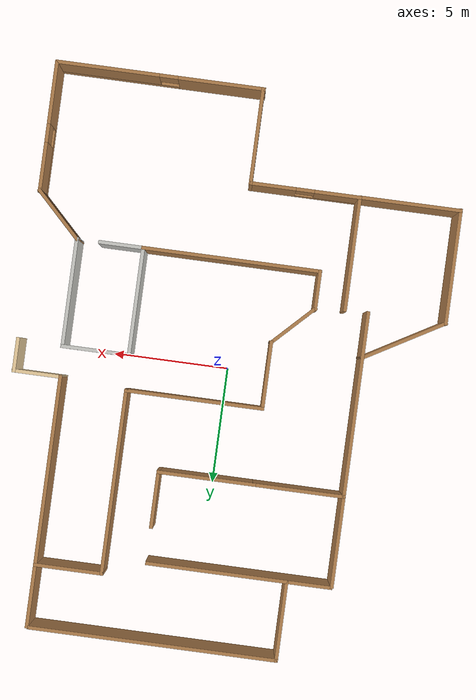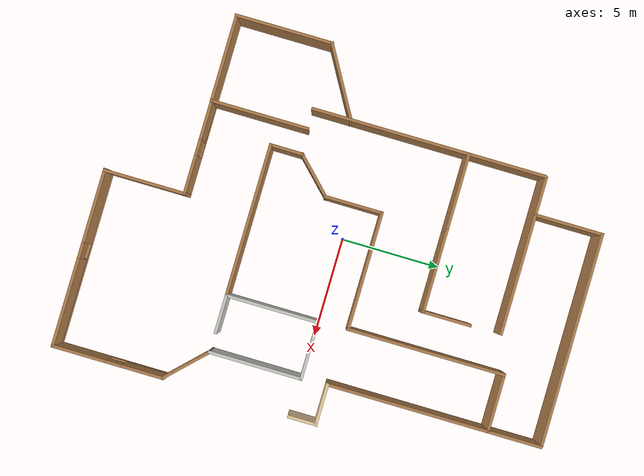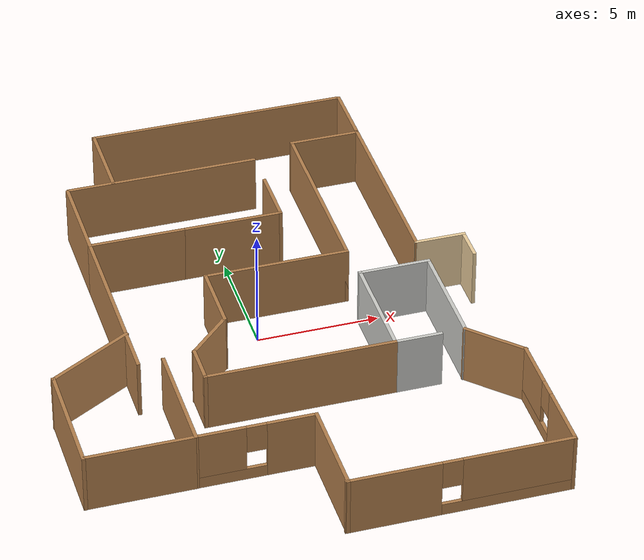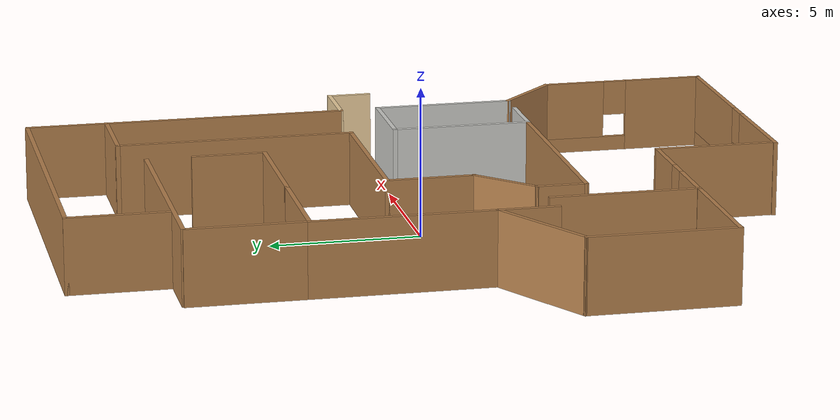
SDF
<?xml version='1.0'?>
<sdf version='1.6'>
  <model name='myHouse'>
    <link name='Wall_0'>
      <pose frame=''>0.060223 -9.98751 0 0 0 -1.5708</pose>
      <self_collide>0</self_collide>
      <kinematic>0</kinematic>
      <visual name='Wall_0_Visual'>
        <pose frame=''>0 0 1.25 0 -0 0</pose>
        <geometry>
          <box>
            <size>4.184 0.15 2.5</size>
          </box>
        </geometry>
        <material>
          <script>
            <uri>file://media/materials/scripts/gazebo.material</uri>
            <name>Gazebo/Wood</name>
          </script>
          <ambient>1 1 1 1</ambient>
          <diffuse>1 1 1 1</diffuse>
          <specular>0.2 0.2 0.2 1</specular>
          <emissive>0 0 0 1</emissive>
        </material>
        <meta>
          <layer>0</layer>
        </meta>
        <transparency>0</transparency>
        <cast_shadows>1</cast_shadows>
      </visual>
      <collision name='Wall_0_Collision'>
        <laser_retro>0</laser_retro>
        <max_contacts>10</max_contacts>
        <pose frame=''>0 0 1.25 0 -0 0</pose>
        <geometry>
          <box>
            <size>4.184 0.15 2.5</size>
          </box>
        </geometry>
        <surface>
          <friction>
            <ode>
              <mu>1</mu>
              <mu2>1</mu2>
              <fdir1>0 0 0</fdir1>
              <slip1>0</slip1>
              <slip2>0</slip2>
            </ode>
            <torsional>
              <coefficient>1</coefficient>
              <patch_radius>0</patch_radius>
              <surface_radius>0</surface_radius>
              <use_patch_radius>1</use_patch_radius>
              <ode>
                <slip>0</slip>
              </ode>
            </torsional>
          </friction>
          <bounce>
            <restitution_coefficient>0</restitution_coefficient>
            <threshold>1e+06</threshold>
          </bounce>
          <contact>
            <collide_without_contact>0</collide_without_contact>
            <collide_without_contact_bitmask>1</collide_without_contact_bitmask>
            <collide_bitmask>1</collide_bitmask>
            <ode>
              <soft_cfm>0</soft_cfm>
              <soft_erp>0.2</soft_erp>
              <kp>1e+13</kp>
              <kd>1</kd>
              <max_vel>0.01</max_vel>
              <min_depth>0</min_depth>
            </ode>
            <bullet>
              <split_impulse>1</split_impulse>
              <split_impulse_penetration_threshold>-0.01</split_impulse_penetration_threshold>
              <soft_cfm>0</soft_cfm>
              <soft_erp>0.2</soft_erp>
              <kp>1e+13</kp>
              <kd>1</kd>
            </bullet>
          </contact>
        </surface>
      </collision>
    </link>
    <link name='Wall_1'>
      <pose frame=''>4.45004 -12.0042 0 0 -0 0</pose>
      <self_collide>0</self_collide>
      <kinematic>0</kinematic>
      <visual name='Wall_1_Visual_0'>
        <pose frame=''>-2.62145 0 1.25 0 -0 0</pose>
        <geometry>
          <box>
            <size>3.7571 0.15 2.5</size>
          </box>
        </geometry>
        <material>
          <script>
            <uri>file://media/materials/scripts/gazebo.material</uri>
            <name>Gazebo/Wood</name>
          </script>
          <ambient>1 1 1 1</ambient>
          <diffuse>1 1 1 1</diffuse>
          <specular>0.2 0.2 0.2 1</specular>
          <emissive>0 0 0 1</emissive>
        </material>
        <meta>
          <layer>0</layer>
        </meta>
        <transparency>0</transparency>
        <cast_shadows>1</cast_shadows>
      </visual>
      <visual name='Wall_1_Visual_1'>
        <pose frame=''>1.87855 0 0.25 0 -0 0</pose>
        <geometry>
          <box>
            <size>5.2429 0.15 0.5</size>
          </box>
        </geometry>
        <material>
          <script>
            <uri>file://media/materials/scripts/gazebo.material</uri>
            <name>Gazebo/Wood</name>
          </script>
          <ambient>1 1 1 1</ambient>
          <diffuse>1 1 1 1</diffuse>
          <specular>0.2 0.2 0.2 1</specular>
          <emissive>0 0 0 1</emissive>
        </material>
        <meta>
          <layer>0</layer>
        </meta>
        <transparency>0</transparency>
        <cast_shadows>1</cast_shadows>
      </visual>
      <visual name='Wall_1_Visual_2'>
        <pose frame=''>2.27855 0 1.5 0 -0 0</pose>
        <geometry>
          <box>
            <size>4.4429 0.15 2</size>
          </box>
        </geometry>
        <material>
          <script>
            <uri>file://media/materials/scripts/gazebo.material</uri>
            <name>Gazebo/Wood</name>
          </script>
          <ambient>1 1 1 1</ambient>
          <diffuse>1 1 1 1</diffuse>
          <specular>0.2 0.2 0.2 1</specular>
          <emissive>0 0 0 1</emissive>
        </material>
        <meta>
          <layer>0</layer>
        </meta>
        <transparency>0</transparency>
        <cast_shadows>1</cast_shadows>
      </visual>
      <visual name='Wall_1_Visual_3'>
        <pose frame=''>-0.342896 0 1.9 0 -0 0</pose>
        <geometry>
          <box>
            <size>0.8 0.15 1.2</size>
          </box>
        </geometry>
        <material>
          <script>
            <uri>file://media/materials/scripts/gazebo.material</uri>
            <name>Gazebo/Wood</name>
          </script>
          <ambient>1 1 1 1</ambient>
          <diffuse>1 1 1 1</diffuse>
          <specular>0.2 0.2 0.2 1</specular>
          <emissive>0 0 0 1</emissive>
        </material>
        <meta>
          <layer>0</layer>
        </meta>
        <transparency>0</transparency>
        <cast_shadows>1</cast_shadows>
      </visual>
      <collision name='Wall_1_Collision_0'>
        <laser_retro>0</laser_retro>
        <max_contacts>10</max_contacts>
        <pose frame=''>-2.62145 0 1.25 0 -0 0</pose>
        <geometry>
          <box>
            <size>3.7571 0.15 2.5</size>
          </box>
        </geometry>
        <surface>
          <friction>
            <ode>
              <mu>1</mu>
              <mu2>1</mu2>
              <fdir1>0 0 0</fdir1>
              <slip1>0</slip1>
              <slip2>0</slip2>
            </ode>
            <torsional>
              <coefficient>1</coefficient>
              <patch_radius>0</patch_radius>
              <surface_radius>0</surface_radius>
              <use_patch_radius>1</use_patch_radius>
              <ode>
                <slip>0</slip>
              </ode>
            </torsional>
          </friction>
          <bounce>
            <restitution_coefficient>0</restitution_coefficient>
            <threshold>1e+06</threshold>
          </bounce>
          <contact>
            <collide_without_contact>0</collide_without_contact>
            <collide_without_contact_bitmask>1</collide_without_contact_bitmask>
            <collide_bitmask>1</collide_bitmask>
            <ode>
              <soft_cfm>0</soft_cfm>
              <soft_erp>0.2</soft_erp>
              <kp>1e+13</kp>
              <kd>1</kd>
              <max_vel>0.01</max_vel>
              <min_depth>0</min_depth>
            </ode>
            <bullet>
              <split_impulse>1</split_impulse>
              <split_impulse_penetration_threshold>-0.01</split_impulse_penetration_threshold>
              <soft_cfm>0</soft_cfm>
              <soft_erp>0.2</soft_erp>
              <kp>1e+13</kp>
              <kd>1</kd>
            </bullet>
          </contact>
        </surface>
      </collision>
      <collision name='Wall_1_Collision_1'>
        <laser_retro>0</laser_retro>
        <max_contacts>10</max_contacts>
        <pose frame=''>1.87855 0 0.25 0 -0 0</pose>
        <geometry>
          <box>
            <size>5.2429 0.15 0.5</size>
          </box>
        </geometry>
        <surface>
          <friction>
            <ode>
              <mu>1</mu>
              <mu2>1</mu2>
              <fdir1>0 0 0</fdir1>
              <slip1>0</slip1>
              <slip2>0</slip2>
            </ode>
            <torsional>
              <coefficient>1</coefficient>
              <patch_radius>0</patch_radius>
              <surface_radius>0</surface_radius>
              <use_patch_radius>1</use_patch_radius>
              <ode>
                <slip>0</slip>
              </ode>
            </torsional>
          </friction>
          <bounce>
            <restitution_coefficient>0</restitution_coefficient>
            <threshold>1e+06</threshold>
          </bounce>
          <contact>
            <collide_without_contact>0</collide_without_contact>
            <collide_without_contact_bitmask>1</collide_without_contact_bitmask>
            <collide_bitmask>1</collide_bitmask>
            <ode>
              <soft_cfm>0</soft_cfm>
              <soft_erp>0.2</soft_erp>
              <kp>1e+13</kp>
              <kd>1</kd>
              <max_vel>0.01</max_vel>
              <min_depth>0</min_depth>
            </ode>
            <bullet>
              <split_impulse>1</split_impulse>
              <split_impulse_penetration_threshold>-0.01</split_impulse_penetration_threshold>
              <soft_cfm>0</soft_cfm>
              <soft_erp>0.2</soft_erp>
              <kp>1e+13</kp>
              <kd>1</kd>
            </bullet>
          </contact>
        </surface>
      </collision>
      <collision name='Wall_1_Collision_2'>
        <laser_retro>0</laser_retro>
        <max_contacts>10</max_contacts>
        <pose frame=''>2.27855 0 1.5 0 -0 0</pose>
        <geometry>
          <box>
            <size>4.4429 0.15 2</size>
          </box>
        </geometry>
        <surface>
          <friction>
            <ode>
              <mu>1</mu>
              <mu2>1</mu2>
              <fdir1>0 0 0</fdir1>
              <slip1>0</slip1>
              <slip2>0</slip2>
            </ode>
            <torsional>
              <coefficient>1</coefficient>
              <patch_radius>0</patch_radius>
              <surface_radius>0</surface_radius>
              <use_patch_radius>1</use_patch_radius>
              <ode>
                <slip>0</slip>
              </ode>
            </torsional>
          </friction>
          <bounce>
            <restitution_coefficient>0</restitution_coefficient>
            <threshold>1e+06</threshold>
          </bounce>
          <contact>
            <collide_without_contact>0</collide_without_contact>
            <collide_without_contact_bitmask>1</collide_without_contact_bitmask>
            <collide_bitmask>1</collide_bitmask>
            <ode>
              <soft_cfm>0</soft_cfm>
              <soft_erp>0.2</soft_erp>
              <kp>1e+13</kp>
              <kd>1</kd>
              <max_vel>0.01</max_vel>
              <min_depth>0</min_depth>
            </ode>
            <bullet>
              <split_impulse>1</split_impulse>
              <split_impulse_penetration_threshold>-0.01</split_impulse_penetration_threshold>
              <soft_cfm>0</soft_cfm>
              <soft_erp>0.2</soft_erp>
              <kp>1e+13</kp>
              <kd>1</kd>
            </bullet>
          </contact>
        </surface>
      </collision>
      <collision name='Wall_1_Collision_3'>
        <laser_retro>0</laser_retro>
        <max_contacts>10</max_contacts>
        <pose frame=''>-0.342896 0 1.9 0 -0 0</pose>
        <geometry>
          <box>
            <size>0.8 0.15 1.2</size>
          </box>
        </geometry>
        <surface>
          <friction>
            <ode>
              <mu>1</mu>
              <mu2>1</mu2>
              <fdir1>0 0 0</fdir1>
              <slip1>0</slip1>
              <slip2>0</slip2>
            </ode>
            <torsional>
              <coefficient>1</coefficient>
              <patch_radius>0</patch_radius>
              <surface_radius>0</surface_radius>
              <use_patch_radius>1</use_patch_radius>
              <ode>
                <slip>0</slip>
              </ode>
            </torsional>
          </friction>
          <bounce>
            <restitution_coefficient>0</restitution_coefficient>
            <threshold>1e+06</threshold>
          </bounce>
          <contact>
            <collide_without_contact>0</collide_without_contact>
            <collide_without_contact_bitmask>1</collide_without_contact_bitmask>
            <collide_bitmask>1</collide_bitmask>
            <ode>
              <soft_cfm>0</soft_cfm>
              <soft_erp>0.2</soft_erp>
              <kp>1e+13</kp>
              <kd>1</kd>
              <max_vel>0.01</max_vel>
              <min_depth>0</min_depth>
            </ode>
            <bullet>
              <split_impulse>1</split_impulse>
              <split_impulse_penetration_threshold>-0.01</split_impulse_penetration_threshold>
              <soft_cfm>0</soft_cfm>
              <soft_erp>0.2</soft_erp>
              <kp>1e+13</kp>
              <kd>1</kd>
            </bullet>
          </contact>
        </surface>
      </collision>
    </link>
    <link name='Wall_10'>
      <pose frame=''>-5.63978 0.790812 0 0 -0 1.5708</pose>
      <self_collide>0</self_collide>
      <kinematic>0</kinematic>
      <visual name='Wall_10_Visual'>
        <pose frame=''>0 0 1.25 0 -0 0</pose>
        <geometry>
          <box>
            <size>8.02625 0.15 2.5</size>
          </box>
        </geometry>
        <material>
          <script>
            <uri>file://media/materials/scripts/gazebo.material</uri>
            <name>Gazebo/Wood</name>
          </script>
          <ambient>1 1 1 1</ambient>
          <diffuse>1 1 1 1</diffuse>
          <specular>0.2 0.2 0.2 1</specular>
          <emissive>0 0 0 1</emissive>
        </material>
        <meta>
          <layer>0</layer>
        </meta>
        <transparency>0</transparency>
        <cast_shadows>1</cast_shadows>
      </visual>
      <collision name='Wall_10_Collision'>
        <laser_retro>0</laser_retro>
        <max_contacts>10</max_contacts>
        <pose frame=''>0 0 1.25 0 -0 0</pose>
        <geometry>
          <box>
            <size>8.02625 0.15 2.5</size>
          </box>
        </geometry>
        <surface>
          <friction>
            <ode>
              <mu>1</mu>
              <mu2>1</mu2>
              <fdir1>0 0 0</fdir1>
              <slip1>0</slip1>
              <slip2>0</slip2>
            </ode>
            <torsional>
              <coefficient>1</coefficient>
              <patch_radius>0</patch_radius>
              <surface_radius>0</surface_radius>
              <use_patch_radius>1</use_patch_radius>
              <ode>
                <slip>0</slip>
              </ode>
            </torsional>
          </friction>
          <bounce>
            <restitution_coefficient>0</restitution_coefficient>
            <threshold>1e+06</threshold>
          </bounce>
          <contact>
            <collide_without_contact>0</collide_without_contact>
            <collide_without_contact_bitmask>1</collide_without_contact_bitmask>
            <collide_bitmask>1</collide_bitmask>
            <ode>
              <soft_cfm>0</soft_cfm>
              <soft_erp>0.2</soft_erp>
              <kp>1e+13</kp>
              <kd>1</kd>
              <max_vel>0.01</max_vel>
              <min_depth>0</min_depth>
            </ode>
            <bullet>
              <split_impulse>1</split_impulse>
              <split_impulse_penetration_threshold>-0.01</split_impulse_penetration_threshold>
              <soft_cfm>0</soft_cfm>
              <soft_erp>0.2</soft_erp>
              <kp>1e+13</kp>
              <kd>1</kd>
            </bullet>
          </contact>
        </surface>
      </collision>
    </link>
    <link name='Wall_13'>
      <pose frame=''>-6.79329 -7.98623 0 0 0 -3.14082</pose>
      <self_collide>0</self_collide>
      <kinematic>0</kinematic>
      <visual name='Wall_13_Visual'>
        <pose frame=''>0 0 1.25 0 -0 0</pose>
        <geometry>
          <box>
            <size>4.46127 0.15 2.5</size>
          </box>
        </geometry>
        <material>
          <script>
            <uri>file://media/materials/scripts/gazebo.material</uri>
            <name>Gazebo/Wood</name>
          </script>
          <ambient>1 1 1 1</ambient>
          <diffuse>1 1 1 1</diffuse>
          <specular>0.2 0.2 0.2 1</specular>
          <emissive>0 0 0 1</emissive>
        </material>
        <meta>
          <layer>0</layer>
        </meta>
        <transparency>0</transparency>
        <cast_shadows>1</cast_shadows>
      </visual>
      <collision name='Wall_13_Collision'>
        <laser_retro>0</laser_retro>
        <max_contacts>10</max_contacts>
        <pose frame=''>0 0 1.25 0 -0 0</pose>
        <geometry>
          <box>
            <size>4.46127 0.15 2.5</size>
          </box>
        </geometry>
        <surface>
          <friction>
            <ode>
              <mu>1</mu>
              <mu2>1</mu2>
              <fdir1>0 0 0</fdir1>
              <slip1>0</slip1>
              <slip2>0</slip2>
            </ode>
            <torsional>
              <coefficient>1</coefficient>
              <patch_radius>0</patch_radius>
              <surface_radius>0</surface_radius>
              <use_patch_radius>1</use_patch_radius>
              <ode>
                <slip>0</slip>
              </ode>
            </torsional>
          </friction>
          <bounce>
            <restitution_coefficient>0</restitution_coefficient>
            <threshold>1e+06</threshold>
          </bounce>
          <contact>
            <collide_without_contact>0</collide_without_contact>
            <collide_without_contact_bitmask>1</collide_without_contact_bitmask>
            <collide_bitmask>1</collide_bitmask>
            <ode>
              <soft_cfm>0</soft_cfm>
              <soft_erp>0.2</soft_erp>
              <kp>1e+13</kp>
              <kd>1</kd>
              <max_vel>0.01</max_vel>
              <min_depth>0</min_depth>
            </ode>
            <bullet>
              <split_impulse>1</split_impulse>
              <split_impulse_penetration_threshold>-0.01</split_impulse_penetration_threshold>
              <soft_cfm>0</soft_cfm>
              <soft_erp>0.2</soft_erp>
              <kp>1e+13</kp>
              <kd>1</kd>
            </bullet>
          </contact>
        </surface>
      </collision>
    </link>
    <link name='Wall_14'>
      <pose frame=''>-8.96215 -5.57611 0 0 -0 1.5708</pose>
      <self_collide>0</self_collide>
      <kinematic>0</kinematic>
      <visual name='Wall_14_Visual'>
        <pose frame=''>0 0 1.25 0 -0 0</pose>
        <geometry>
          <box>
            <size>5 0.15 2.5</size>
          </box>
        </geometry>
        <material>
          <script>
            <uri>file://media/materials/scripts/gazebo.material</uri>
            <name>Gazebo/Wood</name>
          </script>
          <ambient>1 1 1 1</ambient>
          <diffuse>1 1 1 1</diffuse>
          <specular>0.2 0.2 0.2 1</specular>
          <emissive>0 0 0 1</emissive>
        </material>
        <meta>
          <layer>0</layer>
        </meta>
        <transparency>0</transparency>
        <cast_shadows>1</cast_shadows>
      </visual>
      <collision name='Wall_14_Collision'>
        <laser_retro>0</laser_retro>
        <max_contacts>10</max_contacts>
        <pose frame=''>0 0 1.25 0 -0 0</pose>
        <geometry>
          <box>
            <size>5 0.15 2.5</size>
          </box>
        </geometry>
        <surface>
          <friction>
            <ode>
              <mu>1</mu>
              <mu2>1</mu2>
              <fdir1>0 0 0</fdir1>
              <slip1>0</slip1>
              <slip2>0</slip2>
            </ode>
            <torsional>
              <coefficient>1</coefficient>
              <patch_radius>0</patch_radius>
              <surface_radius>0</surface_radius>
              <use_patch_radius>1</use_patch_radius>
              <ode>
                <slip>0</slip>
              </ode>
            </torsional>
          </friction>
          <bounce>
            <restitution_coefficient>0</restitution_coefficient>
            <threshold>1e+06</threshold>
          </bounce>
          <contact>
            <collide_without_contact>0</collide_without_contact>
            <collide_without_contact_bitmask>1</collide_without_contact_bitmask>
            <collide_bitmask>1</collide_bitmask>
            <ode>
              <soft_cfm>0</soft_cfm>
              <soft_erp>0.2</soft_erp>
              <kp>1e+13</kp>
              <kd>1</kd>
              <max_vel>0.01</max_vel>
              <min_depth>0</min_depth>
            </ode>
            <bullet>
              <split_impulse>1</split_impulse>
              <split_impulse_penetration_threshold>-0.01</split_impulse_penetration_threshold>
              <soft_cfm>0</soft_cfm>
              <soft_erp>0.2</soft_erp>
              <kp>1e+13</kp>
              <kd>1</kd>
            </bullet>
          </contact>
        </surface>
      </collision>
    </link>
    <link name='Wall_19'>
      <pose frame=''>-7.29505 -2.18861 0 0 -0 0.523599</pose>
      <self_collide>0</self_collide>
      <kinematic>0</kinematic>
      <visual name='Wall_19_Visual'>
        <pose frame=''>0 0 1.25 0 -0 0</pose>
        <geometry>
          <box>
            <size>4 0.15 2.5</size>
          </box>
        </geometry>
        <material>
          <script>
            <uri>file://media/materials/scripts/gazebo.material</uri>
            <name>Gazebo/Wood</name>
          </script>
          <ambient>1 1 1 1</ambient>
          <diffuse>1 1 1 1</diffuse>
          <specular>0.2 0.2 0.2 1</specular>
          <emissive>0 0 0 1</emissive>
        </material>
        <meta>
          <layer>0</layer>
        </meta>
        <transparency>0</transparency>
        <cast_shadows>1</cast_shadows>
      </visual>
      <collision name='Wall_19_Collision'>
        <laser_retro>0</laser_retro>
        <max_contacts>10</max_contacts>
        <pose frame=''>0 0 1.25 0 -0 0</pose>
        <geometry>
          <box>
            <size>4 0.15 2.5</size>
          </box>
        </geometry>
        <surface>
          <friction>
            <ode>
              <mu>1</mu>
              <mu2>1</mu2>
              <fdir1>0 0 0</fdir1>
              <slip1>0</slip1>
              <slip2>0</slip2>
            </ode>
            <torsional>
              <coefficient>1</coefficient>
              <patch_radius>0</patch_radius>
              <surface_radius>0</surface_radius>
              <use_patch_radius>1</use_patch_radius>
              <ode>
                <slip>0</slip>
              </ode>
            </torsional>
          </friction>
          <bounce>
            <restitution_coefficient>0</restitution_coefficient>
            <threshold>1e+06</threshold>
          </bounce>
          <contact>
            <collide_without_contact>0</collide_without_contact>
            <collide_without_contact_bitmask>1</collide_without_contact_bitmask>
            <collide_bitmask>1</collide_bitmask>
            <ode>
              <soft_cfm>0</soft_cfm>
              <soft_erp>0.2</soft_erp>
              <kp>1e+13</kp>
              <kd>1</kd>
              <max_vel>0.01</max_vel>
              <min_depth>0</min_depth>
            </ode>
            <bullet>
              <split_impulse>1</split_impulse>
              <split_impulse_penetration_threshold>-0.01</split_impulse_penetration_threshold>
              <soft_cfm>0</soft_cfm>
              <soft_erp>0.2</soft_erp>
              <kp>1e+13</kp>
              <kd>1</kd>
            </bullet>
          </contact>
        </surface>
      </collision>
    </link>
    <link name='Wall_2'>
      <pose frame=''>8.91022 -9.23751 0 0 -0 1.5708</pose>
      <self_collide>0</self_collide>
      <kinematic>0</kinematic>
      <visual name='Wall_2_Visual_0'>
        <pose frame=''>-1.47369 0 1.25 0 -0 0</pose>
        <geometry>
          <box>
            <size>2.73646 0.15 2.5</size>
          </box>
        </geometry>
        <material>
          <script>
            <uri>file://media/materials/scripts/gazebo.material</uri>
            <name>Gazebo/Wood</name>
          </script>
          <ambient>1 1 1 1</ambient>
          <diffuse>1 1 1 1</diffuse>
          <specular>0.2 0.2 0.2 1</specular>
          <emissive>0 0 0 1</emissive>
        </material>
        <meta>
          <layer>0</layer>
        </meta>
        <transparency>0</transparency>
        <cast_shadows>1</cast_shadows>
      </visual>
      <visual name='Wall_2_Visual_1'>
        <pose frame=''>1.36823 0 0.25 0 -0 0</pose>
        <geometry>
          <box>
            <size>2.94738 0.15 0.5</size>
          </box>
        </geometry>
        <material>
          <script>
            <uri>file://media/materials/scripts/gazebo.material</uri>
            <name>Gazebo/Wood</name>
          </script>
          <ambient>1 1 1 1</ambient>
          <diffuse>1 1 1 1</diffuse>
          <specular>0.2 0.2 0.2 1</specular>
          <emissive>0 0 0 1</emissive>
        </material>
        <meta>
          <layer>0</layer>
        </meta>
        <transparency>0</transparency>
        <cast_shadows>1</cast_shadows>
      </visual>
      <visual name='Wall_2_Visual_2'>
        <pose frame=''>1.76823 0 1.5 0 -0 0</pose>
        <geometry>
          <box>
            <size>2.14738 0.15 2</size>
          </box>
        </geometry>
        <material>
          <script>
            <uri>file://media/materials/scripts/gazebo.material</uri>
            <name>Gazebo/Wood</name>
          </script>
          <ambient>1 1 1 1</ambient>
          <diffuse>1 1 1 1</diffuse>
          <specular>0.2 0.2 0.2 1</specular>
          <emissive>0 0 0 1</emissive>
        </material>
        <meta>
          <layer>0</layer>
        </meta>
        <transparency>0</transparency>
        <cast_shadows>1</cast_shadows>
      </visual>
      <visual name='Wall_2_Visual_3'>
        <pose frame=''>0.294538 0 1.9 0 -0 0</pose>
        <geometry>
          <box>
            <size>0.8 0.15 1.2</size>
          </box>
        </geometry>
        <material>
          <script>
            <uri>file://media/materials/scripts/gazebo.material</uri>
            <name>Gazebo/Wood</name>
          </script>
          <ambient>1 1 1 1</ambient>
          <diffuse>1 1 1 1</diffuse>
          <specular>0.2 0.2 0.2 1</specular>
          <emissive>0 0 0 1</emissive>
        </material>
        <meta>
          <layer>0</layer>
        </meta>
        <transparency>0</transparency>
        <cast_shadows>1</cast_shadows>
      </visual>
      <collision name='Wall_2_Collision_0'>
        <laser_retro>0</laser_retro>
        <max_contacts>10</max_contacts>
        <pose frame=''>-1.47369 0 1.25 0 -0 0</pose>
        <geometry>
          <box>
            <size>2.73646 0.15 2.5</size>
          </box>
        </geometry>
        <surface>
          <friction>
            <ode>
              <mu>1</mu>
              <mu2>1</mu2>
              <fdir1>0 0 0</fdir1>
              <slip1>0</slip1>
              <slip2>0</slip2>
            </ode>
            <torsional>
              <coefficient>1</coefficient>
              <patch_radius>0</patch_radius>
              <surface_radius>0</surface_radius>
              <use_patch_radius>1</use_patch_radius>
              <ode>
                <slip>0</slip>
              </ode>
            </torsional>
          </friction>
          <bounce>
            <restitution_coefficient>0</restitution_coefficient>
            <threshold>1e+06</threshold>
          </bounce>
          <contact>
            <collide_without_contact>0</collide_without_contact>
            <collide_without_contact_bitmask>1</collide_without_contact_bitmask>
            <collide_bitmask>1</collide_bitmask>
            <ode>
              <soft_cfm>0</soft_cfm>
              <soft_erp>0.2</soft_erp>
              <kp>1e+13</kp>
              <kd>1</kd>
              <max_vel>0.01</max_vel>
              <min_depth>0</min_depth>
            </ode>
            <bullet>
              <split_impulse>1</split_impulse>
              <split_impulse_penetration_threshold>-0.01</split_impulse_penetration_threshold>
              <soft_cfm>0</soft_cfm>
              <soft_erp>0.2</soft_erp>
              <kp>1e+13</kp>
              <kd>1</kd>
            </bullet>
          </contact>
        </surface>
      </collision>
      <collision name='Wall_2_Collision_1'>
        <laser_retro>0</laser_retro>
        <max_contacts>10</max_contacts>
        <pose frame=''>1.36823 0 0.25 0 -0 0</pose>
        <geometry>
          <box>
            <size>2.94738 0.15 0.5</size>
          </box>
        </geometry>
        <surface>
          <friction>
            <ode>
              <mu>1</mu>
              <mu2>1</mu2>
              <fdir1>0 0 0</fdir1>
              <slip1>0</slip1>
              <slip2>0</slip2>
            </ode>
            <torsional>
              <coefficient>1</coefficient>
              <patch_radius>0</patch_radius>
              <surface_radius>0</surface_radius>
              <use_patch_radius>1</use_patch_radius>
              <ode>
                <slip>0</slip>
              </ode>
            </torsional>
          </friction>
          <bounce>
            <restitution_coefficient>0</restitution_coefficient>
            <threshold>1e+06</threshold>
          </bounce>
          <contact>
            <collide_without_contact>0</collide_without_contact>
            <collide_without_contact_bitmask>1</collide_without_contact_bitmask>
            <collide_bitmask>1</collide_bitmask>
            <ode>
              <soft_cfm>0</soft_cfm>
              <soft_erp>0.2</soft_erp>
              <kp>1e+13</kp>
              <kd>1</kd>
              <max_vel>0.01</max_vel>
              <min_depth>0</min_depth>
            </ode>
            <bullet>
              <split_impulse>1</split_impulse>
              <split_impulse_penetration_threshold>-0.01</split_impulse_penetration_threshold>
              <soft_cfm>0</soft_cfm>
              <soft_erp>0.2</soft_erp>
              <kp>1e+13</kp>
              <kd>1</kd>
            </bullet>
          </contact>
        </surface>
      </collision>
      <collision name='Wall_2_Collision_2'>
        <laser_retro>0</laser_retro>
        <max_contacts>10</max_contacts>
        <pose frame=''>1.76823 0 1.5 0 -0 0</pose>
        <geometry>
          <box>
            <size>2.14738 0.15 2</size>
          </box>
        </geometry>
        <surface>
          <friction>
            <ode>
              <mu>1</mu>
              <mu2>1</mu2>
              <fdir1>0 0 0</fdir1>
              <slip1>0</slip1>
              <slip2>0</slip2>
            </ode>
            <torsional>
              <coefficient>1</coefficient>
              <patch_radius>0</patch_radius>
              <surface_radius>0</surface_radius>
              <use_patch_radius>1</use_patch_radius>
              <ode>
                <slip>0</slip>
              </ode>
            </torsional>
          </friction>
          <bounce>
            <restitution_coefficient>0</restitution_coefficient>
            <threshold>1e+06</threshold>
          </bounce>
          <contact>
            <collide_without_contact>0</collide_without_contact>
            <collide_without_contact_bitmask>1</collide_without_contact_bitmask>
            <collide_bitmask>1</collide_bitmask>
            <ode>
              <soft_cfm>0</soft_cfm>
              <soft_erp>0.2</soft_erp>
              <kp>1e+13</kp>
              <kd>1</kd>
              <max_vel>0.01</max_vel>
              <min_depth>0</min_depth>
            </ode>
            <bullet>
              <split_impulse>1</split_impulse>
              <split_impulse_penetration_threshold>-0.01</split_impulse_penetration_threshold>
              <soft_cfm>0</soft_cfm>
              <soft_erp>0.2</soft_erp>
              <kp>1e+13</kp>
              <kd>1</kd>
            </bullet>
          </contact>
        </surface>
      </collision>
      <collision name='Wall_2_Collision_3'>
        <laser_retro>0</laser_retro>
        <max_contacts>10</max_contacts>
        <pose frame=''>0.294538 0 1.9 0 -0 0</pose>
        <geometry>
          <box>
            <size>0.8 0.15 1.2</size>
          </box>
        </geometry>
        <surface>
          <friction>
            <ode>
              <mu>1</mu>
              <mu2>1</mu2>
              <fdir1>0 0 0</fdir1>
              <slip1>0</slip1>
              <slip2>0</slip2>
            </ode>
            <torsional>
              <coefficient>1</coefficient>
              <patch_radius>0</patch_radius>
              <surface_radius>0</surface_radius>
              <use_patch_radius>1</use_patch_radius>
              <ode>
                <slip>0</slip>
              </ode>
            </torsional>
          </friction>
          <bounce>
            <restitution_coefficient>0</restitution_coefficient>
            <threshold>1e+06</threshold>
          </bounce>
          <contact>
            <collide_without_contact>0</collide_without_contact>
            <collide_without_contact_bitmask>1</collide_without_contact_bitmask>
            <collide_bitmask>1</collide_bitmask>
            <ode>
              <soft_cfm>0</soft_cfm>
              <soft_erp>0.2</soft_erp>
              <kp>1e+13</kp>
              <kd>1</kd>
              <max_vel>0.01</max_vel>
              <min_depth>0</min_depth>
            </ode>
            <bullet>
              <split_impulse>1</split_impulse>
              <split_impulse_penetration_threshold>-0.01</split_impulse_penetration_threshold>
              <soft_cfm>0</soft_cfm>
              <soft_erp>0.2</soft_erp>
              <kp>1e+13</kp>
              <kd>1</kd>
            </bullet>
          </contact>
        </surface>
      </collision>
    </link>
    <link name='Wall_22'>
      <pose frame=''>5.64675 -0.032335 0 0 -0 3.14159</pose>
      <self_collide>0</self_collide>
      <kinematic>0</kinematic>
      <visual name='Wall_22_Visual'>
        <pose frame=''>0 0 1.25 0 -0 0</pose>
        <geometry>
          <box>
            <size>3 0.15 2.5</size>
          </box>
        </geometry>
        <material>
          <script>
            <uri>file://media/materials/scripts/gazebo.material</uri>
            <name>Gazebo/CeilingTiled</name>
          </script>
          <ambient>0.921569 0.807843 0.615686 1</ambient>
          <diffuse>1 1 1 1</diffuse>
          <specular>0 0 0 1</specular>
          <emissive>0 0 0 1</emissive>
        </material>
        <meta>
          <layer>0</layer>
        </meta>
        <transparency>0</transparency>
        <cast_shadows>1</cast_shadows>
      </visual>
      <collision name='Wall_22_Collision'>
        <laser_retro>0</laser_retro>
        <max_contacts>10</max_contacts>
        <pose frame=''>0 0 1.25 0 -0 0</pose>
        <geometry>
          <box>
            <size>3 0.15 2.5</size>
          </box>
        </geometry>
        <surface>
          <friction>
            <ode>
              <mu>1</mu>
              <mu2>1</mu2>
              <fdir1>0 0 0</fdir1>
              <slip1>0</slip1>
              <slip2>0</slip2>
            </ode>
            <torsional>
              <coefficient>1</coefficient>
              <patch_radius>0</patch_radius>
              <surface_radius>0</surface_radius>
              <use_patch_radius>1</use_patch_radius>
              <ode>
                <slip>0</slip>
              </ode>
            </torsional>
          </friction>
          <bounce>
            <restitution_coefficient>0</restitution_coefficient>
            <threshold>1e+06</threshold>
          </bounce>
          <contact>
            <collide_without_contact>0</collide_without_contact>
            <collide_without_contact_bitmask>1</collide_without_contact_bitmask>
            <collide_bitmask>1</collide_bitmask>
            <ode>
              <soft_cfm>0</soft_cfm>
              <soft_erp>0.2</soft_erp>
              <kp>1e+13</kp>
              <kd>1</kd>
              <max_vel>0.01</max_vel>
              <min_depth>0</min_depth>
            </ode>
            <bullet>
              <split_impulse>1</split_impulse>
              <split_impulse_penetration_threshold>-0.01</split_impulse_penetration_threshold>
              <soft_cfm>0</soft_cfm>
              <soft_erp>0.2</soft_erp>
              <kp>1e+13</kp>
              <kd>1</kd>
            </bullet>
          </contact>
        </surface>
      </collision>
    </link>
    <link name='Wall_23'>
      <pose frame=''>4.22175 -2.33234 0 0 0 -1.5708</pose>
      <self_collide>0</self_collide>
      <kinematic>0</kinematic>
      <visual name='Wall_23_Visual'>
        <pose frame=''>0 0 1.25 0 -0 0</pose>
        <geometry>
          <box>
            <size>4.75 0.15 2.5</size>
          </box>
        </geometry>
        <material>
          <script>
            <uri>file://media/materials/scripts/gazebo.material</uri>
            <name>Gazebo/CeilingTiled</name>
          </script>
          <ambient>0.921569 0.807843 0.615686 1</ambient>
          <diffuse>1 1 1 1</diffuse>
          <specular>0 0 0 1</specular>
          <emissive>0 0 0 1</emissive>
        </material>
        <meta>
          <layer>0</layer>
        </meta>
        <transparency>0</transparency>
        <cast_shadows>1</cast_shadows>
      </visual>
      <collision name='Wall_23_Collision'>
        <laser_retro>0</laser_retro>
        <max_contacts>10</max_contacts>
        <pose frame=''>0 0 1.25 0 -0 0</pose>
        <geometry>
          <box>
            <size>4.75 0.15 2.5</size>
          </box>
        </geometry>
        <surface>
          <friction>
            <ode>
              <mu>1</mu>
              <mu2>1</mu2>
              <fdir1>0 0 0</fdir1>
              <slip1>0</slip1>
              <slip2>0</slip2>
            </ode>
            <torsional>
              <coefficient>1</coefficient>
              <patch_radius>0</patch_radius>
              <surface_radius>0</surface_radius>
              <use_patch_radius>1</use_patch_radius>
              <ode>
                <slip>0</slip>
              </ode>
            </torsional>
          </friction>
          <bounce>
            <restitution_coefficient>0</restitution_coefficient>
            <threshold>1e+06</threshold>
          </bounce>
          <contact>
            <collide_without_contact>0</collide_without_contact>
            <collide_without_contact_bitmask>1</collide_without_contact_bitmask>
            <collide_bitmask>1</collide_bitmask>
            <ode>
              <soft_cfm>0</soft_cfm>
              <soft_erp>0.2</soft_erp>
              <kp>1e+13</kp>
              <kd>1</kd>
              <max_vel>0.01</max_vel>
              <min_depth>0</min_depth>
            </ode>
            <bullet>
              <split_impulse>1</split_impulse>
              <split_impulse_penetration_threshold>-0.01</split_impulse_penetration_threshold>
              <soft_cfm>0</soft_cfm>
              <soft_erp>0.2</soft_erp>
              <kp>1e+13</kp>
              <kd>1</kd>
            </bullet>
          </contact>
        </surface>
      </collision>
    </link>
    <link name='Wall_24'>
      <pose frame=''>0.421746 -4.63234 0 0 -0 3.14159</pose>
      <self_collide>0</self_collide>
      <kinematic>0</kinematic>
      <visual name='Wall_24_Visual'>
        <pose frame=''>0 0 1.25 0 -0 0</pose>
        <geometry>
          <box>
            <size>7.75 0.15 2.5</size>
          </box>
        </geometry>
        <material>
          <script>
            <uri>file://media/materials/scripts/gazebo.material</uri>
            <name>Gazebo/Wood</name>
          </script>
          <ambient>1 1 1 1</ambient>
          <diffuse>1 1 1 1</diffuse>
          <specular>0.2 0.2 0.2 1</specular>
          <emissive>0 0 0 1</emissive>
        </material>
        <meta>
          <layer>0</layer>
        </meta>
        <transparency>0</transparency>
        <cast_shadows>1</cast_shadows>
      </visual>
      <collision name='Wall_24_Collision'>
        <laser_retro>0</laser_retro>
        <max_contacts>10</max_contacts>
        <pose frame=''>0 0 1.25 0 -0 0</pose>
        <geometry>
          <box>
            <size>7.75 0.15 2.5</size>
          </box>
        </geometry>
        <surface>
          <friction>
            <ode>
              <mu>1</mu>
              <mu2>1</mu2>
              <fdir1>0 0 0</fdir1>
              <slip1>0</slip1>
              <slip2>0</slip2>
            </ode>
            <torsional>
              <coefficient>1</coefficient>
              <patch_radius>0</patch_radius>
              <surface_radius>0</surface_radius>
              <use_patch_radius>1</use_patch_radius>
              <ode>
                <slip>0</slip>
              </ode>
            </torsional>
          </friction>
          <bounce>
            <restitution_coefficient>0</restitution_coefficient>
            <threshold>1e+06</threshold>
          </bounce>
          <contact>
            <collide_without_contact>0</collide_without_contact>
            <collide_without_contact_bitmask>1</collide_without_contact_bitmask>
            <collide_bitmask>1</collide_bitmask>
            <ode>
              <soft_cfm>0</soft_cfm>
              <soft_erp>0.2</soft_erp>
              <kp>1e+13</kp>
              <kd>1</kd>
              <max_vel>0.01</max_vel>
              <min_depth>0</min_depth>
            </ode>
            <bullet>
              <split_impulse>1</split_impulse>
              <split_impulse_penetration_threshold>-0.01</split_impulse_penetration_threshold>
              <soft_cfm>0</soft_cfm>
              <soft_erp>0.2</soft_erp>
              <kp>1e+13</kp>
              <kd>1</kd>
            </bullet>
          </contact>
        </surface>
      </collision>
    </link>
    <link name='Wall_25'>
      <pose frame=''>-3.37825 -3.83234 0 0 -0 1.5708</pose>
      <self_collide>0</self_collide>
      <kinematic>0</kinematic>
      <visual name='Wall_25_Visual'>
        <pose frame=''>0 0 1.25 0 -0 0</pose>
        <geometry>
          <box>
            <size>1.75 0.15 2.5</size>
          </box>
        </geometry>
        <material>
          <script>
            <uri>file://media/materials/scripts/gazebo.material</uri>
            <name>Gazebo/Wood</name>
          </script>
          <ambient>1 1 1 1</ambient>
          <diffuse>1 1 1 1</diffuse>
          <specular>0.2 0.2 0.2 1</specular>
          <emissive>0 0 0 1</emissive>
        </material>
        <meta>
          <layer>0</layer>
        </meta>
        <transparency>0</transparency>
        <cast_shadows>1</cast_shadows>
      </visual>
      <collision name='Wall_25_Collision'>
        <laser_retro>0</laser_retro>
        <max_contacts>10</max_contacts>
        <pose frame=''>0 0 1.25 0 -0 0</pose>
        <geometry>
          <box>
            <size>1.75 0.15 2.5</size>
          </box>
        </geometry>
        <surface>
          <friction>
            <ode>
              <mu>1</mu>
              <mu2>1</mu2>
              <fdir1>0 0 0</fdir1>
              <slip1>0</slip1>
              <slip2>0</slip2>
            </ode>
            <torsional>
              <coefficient>1</coefficient>
              <patch_radius>0</patch_radius>
              <surface_radius>0</surface_radius>
              <use_patch_radius>1</use_patch_radius>
              <ode>
                <slip>0</slip>
              </ode>
            </torsional>
          </friction>
          <bounce>
            <restitution_coefficient>0</restitution_coefficient>
            <threshold>1e+06</threshold>
          </bounce>
          <contact>
            <collide_without_contact>0</collide_without_contact>
            <collide_without_contact_bitmask>1</collide_without_contact_bitmask>
            <collide_bitmask>1</collide_bitmask>
            <ode>
              <soft_cfm>0</soft_cfm>
              <soft_erp>0.2</soft_erp>
              <kp>1e+13</kp>
              <kd>1</kd>
              <max_vel>0.01</max_vel>
              <min_depth>0</min_depth>
            </ode>
            <bullet>
              <split_impulse>1</split_impulse>
              <split_impulse_penetration_threshold>-0.01</split_impulse_penetration_threshold>
              <soft_cfm>0</soft_cfm>
              <soft_erp>0.2</soft_erp>
              <kp>1e+13</kp>
              <kd>1</kd>
            </bullet>
          </contact>
        </surface>
      </collision>
    </link>
    <link name='Wall_26'>
      <pose frame=''>-2.5474 -2.20148 0 0 -0 0.785398</pose>
      <self_collide>0</self_collide>
      <kinematic>0</kinematic>
      <visual name='Wall_26_Visual'>
        <pose frame=''>0 0 1.25 0 -0 0</pose>
        <geometry>
          <box>
            <size>2.5 0.15 2.5</size>
          </box>
        </geometry>
        <material>
          <script>
            <uri>file://media/materials/scripts/gazebo.material</uri>
            <name>Gazebo/Wood</name>
          </script>
          <ambient>1 1 1 1</ambient>
          <diffuse>1 1 1 1</diffuse>
          <specular>0.2 0.2 0.2 1</specular>
          <emissive>0 0 0 1</emissive>
        </material>
        <meta>
          <layer>0</layer>
        </meta>
        <transparency>0</transparency>
        <cast_shadows>1</cast_shadows>
      </visual>
      <collision name='Wall_26_Collision'>
        <laser_retro>0</laser_retro>
        <max_contacts>10</max_contacts>
        <pose frame=''>0 0 1.25 0 -0 0</pose>
        <geometry>
          <box>
            <size>2.5 0.15 2.5</size>
          </box>
        </geometry>
        <surface>
          <friction>
            <ode>
              <mu>1</mu>
              <mu2>1</mu2>
              <fdir1>0 0 0</fdir1>
              <slip1>0</slip1>
              <slip2>0</slip2>
            </ode>
            <torsional>
              <coefficient>1</coefficient>
              <patch_radius>0</patch_radius>
              <surface_radius>0</surface_radius>
              <use_patch_radius>1</use_patch_radius>
              <ode>
                <slip>0</slip>
              </ode>
            </torsional>
          </friction>
          <bounce>
            <restitution_coefficient>0</restitution_coefficient>
            <threshold>1e+06</threshold>
          </bounce>
          <contact>
            <collide_without_contact>0</collide_without_contact>
            <collide_without_contact_bitmask>1</collide_without_contact_bitmask>
            <collide_bitmask>1</collide_bitmask>
            <ode>
              <soft_cfm>0</soft_cfm>
              <soft_erp>0.2</soft_erp>
              <kp>1e+13</kp>
              <kd>1</kd>
              <max_vel>0.01</max_vel>
              <min_depth>0</min_depth>
            </ode>
            <bullet>
              <split_impulse>1</split_impulse>
              <split_impulse_penetration_threshold>-0.01</split_impulse_penetration_threshold>
              <soft_cfm>0</soft_cfm>
              <soft_erp>0.2</soft_erp>
              <kp>1e+13</kp>
              <kd>1</kd>
            </bullet>
          </contact>
        </surface>
      </collision>
    </link>
    <link name='Wall_27'>
      <pose frame=''>-1.71655 0.054366 0 0 -0 1.5708</pose>
      <self_collide>0</self_collide>
      <kinematic>0</kinematic>
      <visual name='Wall_27_Visual'>
        <pose frame=''>0 0 1.25 0 -0 0</pose>
        <geometry>
          <box>
            <size>3 0.15 2.5</size>
          </box>
        </geometry>
        <material>
          <script>
            <uri>file://media/materials/scripts/gazebo.material</uri>
            <name>Gazebo/Wood</name>
          </script>
          <ambient>1 1 1 1</ambient>
          <diffuse>1 1 1 1</diffuse>
          <specular>0.2 0.2 0.2 1</specular>
          <emissive>0 0 0 1</emissive>
        </material>
        <meta>
          <layer>0</layer>
        </meta>
        <transparency>0</transparency>
        <cast_shadows>1</cast_shadows>
      </visual>
      <collision name='Wall_27_Collision'>
        <laser_retro>0</laser_retro>
        <max_contacts>10</max_contacts>
        <pose frame=''>0 0 1.25 0 -0 0</pose>
        <geometry>
          <box>
            <size>3 0.15 2.5</size>
          </box>
        </geometry>
        <surface>
          <friction>
            <ode>
              <mu>1</mu>
              <mu2>1</mu2>
              <fdir1>0 0 0</fdir1>
              <slip1>0</slip1>
              <slip2>0</slip2>
            </ode>
            <torsional>
              <coefficient>1</coefficient>
              <patch_radius>0</patch_radius>
              <surface_radius>0</surface_radius>
              <use_patch_radius>1</use_patch_radius>
              <ode>
                <slip>0</slip>
              </ode>
            </torsional>
          </friction>
          <bounce>
            <restitution_coefficient>0</restitution_coefficient>
            <threshold>1e+06</threshold>
          </bounce>
          <contact>
            <collide_without_contact>0</collide_without_contact>
            <collide_without_contact_bitmask>1</collide_without_contact_bitmask>
            <collide_bitmask>1</collide_bitmask>
            <ode>
              <soft_cfm>0</soft_cfm>
              <soft_erp>0.2</soft_erp>
              <kp>1e+13</kp>
              <kd>1</kd>
              <max_vel>0.01</max_vel>
              <min_depth>0</min_depth>
            </ode>
            <bullet>
              <split_impulse>1</split_impulse>
              <split_impulse_penetration_threshold>-0.01</split_impulse_penetration_threshold>
              <soft_cfm>0</soft_cfm>
              <soft_erp>0.2</soft_erp>
              <kp>1e+13</kp>
              <kd>1</kd>
            </bullet>
          </contact>
        </surface>
      </collision>
    </link>
    <link name='Wall_28'>
      <pose frame=''>1.20845 1.47937 0 0 -0 0</pose>
      <self_collide>0</self_collide>
      <kinematic>0</kinematic>
      <visual name='Wall_28_Visual'>
        <pose frame=''>0 0 1.25 0 -0 0</pose>
        <geometry>
          <box>
            <size>6 0.15 2.5</size>
          </box>
        </geometry>
        <material>
          <script>
            <uri>file://media/materials/scripts/gazebo.material</uri>
            <name>Gazebo/Wood</name>
          </script>
          <ambient>1 1 1 1</ambient>
          <diffuse>1 1 1 1</diffuse>
          <specular>0.2 0.2 0.2 1</specular>
          <emissive>0 0 0 1</emissive>
        </material>
        <meta>
          <layer>0</layer>
        </meta>
        <transparency>0</transparency>
        <cast_shadows>1</cast_shadows>
      </visual>
      <collision name='Wall_28_Collision'>
        <laser_retro>0</laser_retro>
        <max_contacts>10</max_contacts>
        <pose frame=''>0 0 1.25 0 -0 0</pose>
        <geometry>
          <box>
            <size>6 0.15 2.5</size>
          </box>
        </geometry>
        <surface>
          <friction>
            <ode>
              <mu>1</mu>
              <mu2>1</mu2>
              <fdir1>0 0 0</fdir1>
              <slip1>0</slip1>
              <slip2>0</slip2>
            </ode>
            <torsional>
              <coefficient>1</coefficient>
              <patch_radius>0</patch_radius>
              <surface_radius>0</surface_radius>
              <use_patch_radius>1</use_patch_radius>
              <ode>
                <slip>0</slip>
              </ode>
            </torsional>
          </friction>
          <bounce>
            <restitution_coefficient>0</restitution_coefficient>
            <threshold>1e+06</threshold>
          </bounce>
          <contact>
            <collide_without_contact>0</collide_without_contact>
            <collide_without_contact_bitmask>1</collide_without_contact_bitmask>
            <collide_bitmask>1</collide_bitmask>
            <ode>
              <soft_cfm>0</soft_cfm>
              <soft_erp>0.2</soft_erp>
              <kp>1e+13</kp>
              <kd>1</kd>
              <max_vel>0.01</max_vel>
              <min_depth>0</min_depth>
            </ode>
            <bullet>
              <split_impulse>1</split_impulse>
              <split_impulse_penetration_threshold>-0.01</split_impulse_penetration_threshold>
              <soft_cfm>0</soft_cfm>
              <soft_erp>0.2</soft_erp>
              <kp>1e+13</kp>
              <kd>1</kd>
            </bullet>
          </contact>
        </surface>
      </collision>
    </link>
    <link name='Wall_29'>
      <pose frame=''>4.13345 5.40437 0 0 -0 1.5708</pose>
      <self_collide>0</self_collide>
      <kinematic>0</kinematic>
      <visual name='Wall_29_Visual'>
        <pose frame=''>0 0 1.25 0 -0 0</pose>
        <geometry>
          <box>
            <size>8 0.15 2.5</size>
          </box>
        </geometry>
        <material>
          <script>
            <uri>file://media/materials/scripts/gazebo.material</uri>
            <name>Gazebo/Wood</name>
          </script>
          <ambient>1 1 1 1</ambient>
          <diffuse>1 1 1 1</diffuse>
          <specular>0.2 0.2 0.2 1</specular>
          <emissive>0 0 0 1</emissive>
        </material>
        <meta>
          <layer>0</layer>
        </meta>
        <transparency>0</transparency>
        <cast_shadows>1</cast_shadows>
      </visual>
      <collision name='Wall_29_Collision'>
        <laser_retro>0</laser_retro>
        <max_contacts>10</max_contacts>
        <pose frame=''>0 0 1.25 0 -0 0</pose>
        <geometry>
          <box>
            <size>8 0.15 2.5</size>
          </box>
        </geometry>
        <surface>
          <friction>
            <ode>
              <mu>1</mu>
              <mu2>1</mu2>
              <fdir1>0 0 0</fdir1>
              <slip1>0</slip1>
              <slip2>0</slip2>
            </ode>
            <torsional>
              <coefficient>1</coefficient>
              <patch_radius>0</patch_radius>
              <surface_radius>0</surface_radius>
              <use_patch_radius>1</use_patch_radius>
              <ode>
                <slip>0</slip>
              </ode>
            </torsional>
          </friction>
          <bounce>
            <restitution_coefficient>0</restitution_coefficient>
            <threshold>1e+06</threshold>
          </bounce>
          <contact>
            <collide_without_contact>0</collide_without_contact>
            <collide_without_contact_bitmask>1</collide_without_contact_bitmask>
            <collide_bitmask>1</collide_bitmask>
            <ode>
              <soft_cfm>0</soft_cfm>
              <soft_erp>0.2</soft_erp>
              <kp>1e+13</kp>
              <kd>1</kd>
              <max_vel>0.01</max_vel>
              <min_depth>0</min_depth>
            </ode>
            <bullet>
              <split_impulse>1</split_impulse>
              <split_impulse_penetration_threshold>-0.01</split_impulse_penetration_threshold>
              <soft_cfm>0</soft_cfm>
              <soft_erp>0.2</soft_erp>
              <kp>1e+13</kp>
              <kd>1</kd>
            </bullet>
          </contact>
        </surface>
      </collision>
    </link>
    <link name='Wall_3'>
      <pose frame=''>7.99098 -5.55157 0 0 -0 2.35619</pose>
      <self_collide>0</self_collide>
      <kinematic>0</kinematic>
      <visual name='Wall_3_Visual'>
        <pose frame=''>0 0 1.25 0 -0 0</pose>
        <geometry>
          <box>
            <size>2.75 0.15 2.5</size>
          </box>
        </geometry>
        <material>
          <script>
            <uri>file://media/materials/scripts/gazebo.material</uri>
            <name>Gazebo/Wood</name>
          </script>
          <ambient>1 1 1 1</ambient>
          <diffuse>1 1 1 1</diffuse>
          <specular>0.2 0.2 0.2 1</specular>
          <emissive>0 0 0 1</emissive>
        </material>
        <meta>
          <layer>0</layer>
        </meta>
        <transparency>0</transparency>
        <cast_shadows>1</cast_shadows>
      </visual>
      <collision name='Wall_3_Collision'>
        <laser_retro>0</laser_retro>
        <max_contacts>10</max_contacts>
        <pose frame=''>0 0 1.25 0 -0 0</pose>
        <geometry>
          <box>
            <size>2.75 0.15 2.5</size>
          </box>
        </geometry>
        <surface>
          <friction>
            <ode>
              <mu>1</mu>
              <mu2>1</mu2>
              <fdir1>0 0 0</fdir1>
              <slip1>0</slip1>
              <slip2>0</slip2>
            </ode>
            <torsional>
              <coefficient>1</coefficient>
              <patch_radius>0</patch_radius>
              <surface_radius>0</surface_radius>
              <use_patch_radius>1</use_patch_radius>
              <ode>
                <slip>0</slip>
              </ode>
            </torsional>
          </friction>
          <bounce>
            <restitution_coefficient>0</restitution_coefficient>
            <threshold>1e+06</threshold>
          </bounce>
          <contact>
            <collide_without_contact>0</collide_without_contact>
            <collide_without_contact_bitmask>1</collide_without_contact_bitmask>
            <collide_bitmask>1</collide_bitmask>
            <ode>
              <soft_cfm>0</soft_cfm>
              <soft_erp>0.2</soft_erp>
              <kp>1e+13</kp>
              <kd>1</kd>
              <max_vel>0.01</max_vel>
              <min_depth>0</min_depth>
            </ode>
            <bullet>
              <split_impulse>1</split_impulse>
              <split_impulse_penetration_threshold>-0.01</split_impulse_penetration_threshold>
              <soft_cfm>0</soft_cfm>
              <soft_erp>0.2</soft_erp>
              <kp>1e+13</kp>
              <kd>1</kd>
            </bullet>
          </contact>
        </surface>
      </collision>
    </link>
    <link name='Wall_30'>
      <pose frame=''>5.55565 9.3284 0 0 0 -0.000679</pose>
      <self_collide>0</self_collide>
      <kinematic>0</kinematic>
      <visual name='Wall_30_Visual'>
        <pose frame=''>0 0 1.25 0 -0 0</pose>
        <geometry>
          <box>
            <size>2.99474 0.15 2.5</size>
          </box>
        </geometry>
        <material>
          <script>
            <uri>file://media/materials/scripts/gazebo.material</uri>
            <name>Gazebo/Wood</name>
          </script>
          <ambient>1 1 1 1</ambient>
          <diffuse>1 1 1 1</diffuse>
          <specular>0.2 0.2 0.2 1</specular>
          <emissive>0 0 0 1</emissive>
        </material>
        <meta>
          <layer>0</layer>
        </meta>
        <transparency>0</transparency>
        <cast_shadows>1</cast_shadows>
      </visual>
      <collision name='Wall_30_Collision'>
        <laser_retro>0</laser_retro>
        <max_contacts>10</max_contacts>
        <pose frame=''>0 0 1.25 0 -0 0</pose>
        <geometry>
          <box>
            <size>2.99474 0.15 2.5</size>
          </box>
        </geometry>
        <surface>
          <friction>
            <ode>
              <mu>1</mu>
              <mu2>1</mu2>
              <fdir1>0 0 0</fdir1>
              <slip1>0</slip1>
              <slip2>0</slip2>
            </ode>
            <torsional>
              <coefficient>1</coefficient>
              <patch_radius>0</patch_radius>
              <surface_radius>0</surface_radius>
              <use_patch_radius>1</use_patch_radius>
              <ode>
                <slip>0</slip>
              </ode>
            </torsional>
          </friction>
          <bounce>
            <restitution_coefficient>0</restitution_coefficient>
            <threshold>1e+06</threshold>
          </bounce>
          <contact>
            <collide_without_contact>0</collide_without_contact>
            <collide_without_contact_bitmask>1</collide_without_contact_bitmask>
            <collide_bitmask>1</collide_bitmask>
            <ode>
              <soft_cfm>0</soft_cfm>
              <soft_erp>0.2</soft_erp>
              <kp>1e+13</kp>
              <kd>1</kd>
              <max_vel>0.01</max_vel>
              <min_depth>0</min_depth>
            </ode>
            <bullet>
              <split_impulse>1</split_impulse>
              <split_impulse_penetration_threshold>-0.01</split_impulse_penetration_threshold>
              <soft_cfm>0</soft_cfm>
              <soft_erp>0.2</soft_erp>
              <kp>1e+13</kp>
              <kd>1</kd>
            </bullet>
          </contact>
        </surface>
      </collision>
    </link>
    <link name='Wall_31'>
      <pose frame=''>6.97785 5.3228 0 0 0 -1.5708</pose>
      <self_collide>0</self_collide>
      <kinematic>0</kinematic>
      <visual name='Wall_31_Visual'>
        <pose frame=''>0 0 1.25 0 -0 0</pose>
        <geometry>
          <box>
            <size>8.25 0.15 2.5</size>
          </box>
        </geometry>
        <material>
          <script>
            <uri>file://media/materials/scripts/gazebo.material</uri>
            <name>Gazebo/Wood</name>
          </script>
          <ambient>1 1 1 1</ambient>
          <diffuse>1 1 1 1</diffuse>
          <specular>0.2 0.2 0.2 1</specular>
          <emissive>0 0 0 1</emissive>
        </material>
        <meta>
          <layer>0</layer>
        </meta>
        <transparency>0</transparency>
        <cast_shadows>1</cast_shadows>
      </visual>
      <collision name='Wall_31_Collision'>
        <laser_retro>0</laser_retro>
        <max_contacts>10</max_contacts>
        <pose frame=''>0 0 1.25 0 -0 0</pose>
        <geometry>
          <box>
            <size>8.25 0.15 2.5</size>
          </box>
        </geometry>
        <surface>
          <friction>
            <ode>
              <mu>1</mu>
              <mu2>1</mu2>
              <fdir1>0 0 0</fdir1>
              <slip1>0</slip1>
              <slip2>0</slip2>
            </ode>
            <torsional>
              <coefficient>1</coefficient>
              <patch_radius>0</patch_radius>
              <surface_radius>0</surface_radius>
              <use_patch_radius>1</use_patch_radius>
              <ode>
                <slip>0</slip>
              </ode>
            </torsional>
          </friction>
          <bounce>
            <restitution_coefficient>0</restitution_coefficient>
            <threshold>1e+06</threshold>
          </bounce>
          <contact>
            <collide_without_contact>0</collide_without_contact>
            <collide_without_contact_bitmask>1</collide_without_contact_bitmask>
            <collide_bitmask>1</collide_bitmask>
            <ode>
              <soft_cfm>0</soft_cfm>
              <soft_erp>0.2</soft_erp>
              <kp>1e+13</kp>
              <kd>1</kd>
              <max_vel>0.01</max_vel>
              <min_depth>0</min_depth>
            </ode>
            <bullet>
              <split_impulse>1</split_impulse>
              <split_impulse_penetration_threshold>-0.01</split_impulse_penetration_threshold>
              <soft_cfm>0</soft_cfm>
              <soft_erp>0.2</soft_erp>
              <kp>1e+13</kp>
              <kd>1</kd>
            </bullet>
          </contact>
        </surface>
      </collision>
    </link>
    <link name='Wall_37'>
      <pose frame=''>-3.71478 4.72896 0 0 -0 0.000116</pose>
      <self_collide>0</self_collide>
      <kinematic>0</kinematic>
      <visual name='Wall_37_Visual'>
        <pose frame=''>0 0 1.25 0 -0 0</pose>
        <geometry>
          <box>
            <size>4 0.15 2.5</size>
          </box>
        </geometry>
        <material>
          <script>
            <uri>file://media/materials/scripts/gazebo.material</uri>
            <name>Gazebo/Wood</name>
          </script>
          <ambient>1 1 1 1</ambient>
          <diffuse>1 1 1 1</diffuse>
          <specular>0.2 0.2 0.2 1</specular>
          <emissive>0 0 0 1</emissive>
        </material>
        <meta>
          <layer>0</layer>
        </meta>
        <transparency>0</transparency>
        <cast_shadows>1</cast_shadows>
      </visual>
      <collision name='Wall_37_Collision'>
        <laser_retro>0</laser_retro>
        <max_contacts>10</max_contacts>
        <pose frame=''>0 0 1.25 0 -0 0</pose>
        <geometry>
          <box>
            <size>4 0.15 2.5</size>
          </box>
        </geometry>
        <surface>
          <friction>
            <ode>
              <mu>1</mu>
              <mu2>1</mu2>
              <fdir1>0 0 0</fdir1>
              <slip1>0</slip1>
              <slip2>0</slip2>
            </ode>
            <torsional>
              <coefficient>1</coefficient>
              <patch_radius>0</patch_radius>
              <surface_radius>0</surface_radius>
              <use_patch_radius>1</use_patch_radius>
              <ode>
                <slip>0</slip>
              </ode>
            </torsional>
          </friction>
          <bounce>
            <restitution_coefficient>0</restitution_coefficient>
            <threshold>1e+06</threshold>
          </bounce>
          <contact>
            <collide_without_contact>0</collide_without_contact>
            <collide_without_contact_bitmask>1</collide_without_contact_bitmask>
            <collide_bitmask>1</collide_bitmask>
            <ode>
              <soft_cfm>0</soft_cfm>
              <soft_erp>0.2</soft_erp>
              <kp>1e+13</kp>
              <kd>1</kd>
              <max_vel>0.01</max_vel>
              <min_depth>0</min_depth>
            </ode>
            <bullet>
              <split_impulse>1</split_impulse>
              <split_impulse_penetration_threshold>-0.01</split_impulse_penetration_threshold>
              <soft_cfm>0</soft_cfm>
              <soft_erp>0.2</soft_erp>
              <kp>1e+13</kp>
              <kd>1</kd>
            </bullet>
          </contact>
        </surface>
      </collision>
    </link>
    <link name='Wall_38'>
      <pose frame=''>0.260223 4.72919 0 0 -0 0</pose>
      <self_collide>0</self_collide>
      <kinematic>0</kinematic>
      <visual name='Wall_38_Visual'>
        <pose frame=''>0 0 1.25 0 -0 0</pose>
        <geometry>
          <box>
            <size>4.25 0.15 2.5</size>
          </box>
        </geometry>
        <material>
          <script>
            <uri>file://media/materials/scripts/gazebo.material</uri>
            <name>Gazebo/Wood</name>
          </script>
          <ambient>1 1 1 1</ambient>
          <diffuse>1 1 1 1</diffuse>
          <specular>0.2 0.2 0.2 1</specular>
          <emissive>0 0 0 1</emissive>
        </material>
        <meta>
          <layer>0</layer>
        </meta>
        <transparency>0</transparency>
        <cast_shadows>1</cast_shadows>
      </visual>
      <collision name='Wall_38_Collision'>
        <laser_retro>0</laser_retro>
        <max_contacts>10</max_contacts>
        <pose frame=''>0 0 1.25 0 -0 0</pose>
        <geometry>
          <box>
            <size>4.25 0.15 2.5</size>
          </box>
        </geometry>
        <surface>
          <friction>
            <ode>
              <mu>1</mu>
              <mu2>1</mu2>
              <fdir1>0 0 0</fdir1>
              <slip1>0</slip1>
              <slip2>0</slip2>
            </ode>
            <torsional>
              <coefficient>1</coefficient>
              <patch_radius>0</patch_radius>
              <surface_radius>0</surface_radius>
              <use_patch_radius>1</use_patch_radius>
              <ode>
                <slip>0</slip>
              </ode>
            </torsional>
          </friction>
          <bounce>
            <restitution_coefficient>0</restitution_coefficient>
            <threshold>1e+06</threshold>
          </bounce>
          <contact>
            <collide_without_contact>0</collide_without_contact>
            <collide_without_contact_bitmask>1</collide_without_contact_bitmask>
            <collide_bitmask>1</collide_bitmask>
            <ode>
              <soft_cfm>0</soft_cfm>
              <soft_erp>0.2</soft_erp>
              <kp>1e+13</kp>
              <kd>1</kd>
              <max_vel>0.01</max_vel>
              <min_depth>0</min_depth>
            </ode>
            <bullet>
              <split_impulse>1</split_impulse>
              <split_impulse_penetration_threshold>-0.01</split_impulse_penetration_threshold>
              <soft_cfm>0</soft_cfm>
              <soft_erp>0.2</soft_erp>
              <kp>1e+13</kp>
              <kd>1</kd>
            </bullet>
          </contact>
        </surface>
      </collision>
    </link>
    <link name='Wall_39'>
      <pose frame=''>2.31022 5.90419 0 0 -0 1.5708</pose>
      <self_collide>0</self_collide>
      <kinematic>0</kinematic>
      <visual name='Wall_39_Visual'>
        <pose frame=''>0 0 1.25 0 -0 0</pose>
        <geometry>
          <box>
            <size>2.5 0.15 2.5</size>
          </box>
        </geometry>
        <material>
          <script>
            <uri>file://media/materials/scripts/gazebo.material</uri>
            <name>Gazebo/Wood</name>
          </script>
          <ambient>1 1 1 1</ambient>
          <diffuse>1 1 1 1</diffuse>
          <specular>0.2 0.2 0.2 1</specular>
          <emissive>0 0 0 1</emissive>
        </material>
        <meta>
          <layer>0</layer>
        </meta>
        <transparency>0</transparency>
        <cast_shadows>1</cast_shadows>
      </visual>
      <collision name='Wall_39_Collision'>
        <laser_retro>0</laser_retro>
        <max_contacts>10</max_contacts>
        <pose frame=''>0 0 1.25 0 -0 0</pose>
        <geometry>
          <box>
            <size>2.5 0.15 2.5</size>
          </box>
        </geometry>
        <surface>
          <friction>
            <ode>
              <mu>1</mu>
              <mu2>1</mu2>
              <fdir1>0 0 0</fdir1>
              <slip1>0</slip1>
              <slip2>0</slip2>
            </ode>
            <torsional>
              <coefficient>1</coefficient>
              <patch_radius>0</patch_radius>
              <surface_radius>0</surface_radius>
              <use_patch_radius>1</use_patch_radius>
              <ode>
                <slip>0</slip>
              </ode>
            </torsional>
          </friction>
          <bounce>
            <restitution_coefficient>0</restitution_coefficient>
            <threshold>1e+06</threshold>
          </bounce>
          <contact>
            <collide_without_contact>0</collide_without_contact>
            <collide_without_contact_bitmask>1</collide_without_contact_bitmask>
            <collide_bitmask>1</collide_bitmask>
            <ode>
              <soft_cfm>0</soft_cfm>
              <soft_erp>0.2</soft_erp>
              <kp>1e+13</kp>
              <kd>1</kd>
              <max_vel>0.01</max_vel>
              <min_depth>0</min_depth>
            </ode>
            <bullet>
              <split_impulse>1</split_impulse>
              <split_impulse_penetration_threshold>-0.01</split_impulse_penetration_threshold>
              <soft_cfm>0</soft_cfm>
              <soft_erp>0.2</soft_erp>
              <kp>1e+13</kp>
              <kd>1</kd>
            </bullet>
          </contact>
        </surface>
      </collision>
    </link>
    <link name='Wall_4'>
      <pose frame=''>7.07175 -2.33234 0 0 -0 1.5708</pose>
      <self_collide>0</self_collide>
      <kinematic>0</kinematic>
      <visual name='Wall_4_Visual'>
        <pose frame=''>0 0 1.25 0 -0 0</pose>
        <geometry>
          <box>
            <size>4.75 0.15 2.5</size>
          </box>
        </geometry>
        <material>
          <script>
            <uri>file://media/materials/scripts/gazebo.material</uri>
            <name>Gazebo/CeilingTiled</name>
          </script>
          <ambient>0.921569 0.807843 0.615686 1</ambient>
          <diffuse>1 1 1 1</diffuse>
          <specular>0 0 0 1</specular>
          <emissive>0 0 0 1</emissive>
        </material>
        <meta>
          <layer>0</layer>
        </meta>
        <transparency>0</transparency>
        <cast_shadows>1</cast_shadows>
      </visual>
      <collision name='Wall_4_Collision'>
        <laser_retro>0</laser_retro>
        <max_contacts>10</max_contacts>
        <pose frame=''>0 0 1.25 0 -0 0</pose>
        <geometry>
          <box>
            <size>4.75 0.15 2.5</size>
          </box>
        </geometry>
        <surface>
          <friction>
            <ode>
              <mu>1</mu>
              <mu2>1</mu2>
              <fdir1>0 0 0</fdir1>
              <slip1>0</slip1>
              <slip2>0</slip2>
            </ode>
            <torsional>
              <coefficient>1</coefficient>
              <patch_radius>0</patch_radius>
              <surface_radius>0</surface_radius>
              <use_patch_radius>1</use_patch_radius>
              <ode>
                <slip>0</slip>
              </ode>
            </torsional>
          </friction>
          <bounce>
            <restitution_coefficient>0</restitution_coefficient>
            <threshold>1e+06</threshold>
          </bounce>
          <contact>
            <collide_without_contact>0</collide_without_contact>
            <collide_without_contact_bitmask>1</collide_without_contact_bitmask>
            <collide_bitmask>1</collide_bitmask>
            <ode>
              <soft_cfm>0</soft_cfm>
              <soft_erp>0.2</soft_erp>
              <kp>1e+13</kp>
              <kd>1</kd>
              <max_vel>0.01</max_vel>
              <min_depth>0</min_depth>
            </ode>
            <bullet>
              <split_impulse>1</split_impulse>
              <split_impulse_penetration_threshold>-0.01</split_impulse_penetration_threshold>
              <soft_cfm>0</soft_cfm>
              <soft_erp>0.2</soft_erp>
              <kp>1e+13</kp>
              <kd>1</kd>
            </bullet>
          </contact>
        </surface>
      </collision>
    </link>
    <link name='Wall_41'>
      <pose frame=''>-1.66015 8.63454 0 0 0 -3.14154</pose>
      <self_collide>0</self_collide>
      <kinematic>0</kinematic>
      <visual name='Wall_41_Visual'>
        <pose frame=''>0 0 1.25 0 -0 0</pose>
        <geometry>
          <box>
            <size>8 0.15 2.5</size>
          </box>
        </geometry>
        <material>
          <script>
            <uri>file://media/materials/scripts/gazebo.material</uri>
            <name>Gazebo/Wood</name>
          </script>
          <ambient>0.921569 0.807843 0.615686 1</ambient>
          <diffuse>1 1 1 1</diffuse>
          <specular>0.2 0.2 0.2 1</specular>
          <emissive>0 0 0 1</emissive>
        </material>
        <meta>
          <layer>0</layer>
        </meta>
        <transparency>0</transparency>
        <cast_shadows>1</cast_shadows>
      </visual>
      <collision name='Wall_41_Collision'>
        <laser_retro>0</laser_retro>
        <max_contacts>10</max_contacts>
        <pose frame=''>0 0 1.25 0 -0 0</pose>
        <geometry>
          <box>
            <size>8 0.15 2.5</size>
          </box>
        </geometry>
        <surface>
          <friction>
            <ode>
              <mu>1</mu>
              <mu2>1</mu2>
              <fdir1>0 0 0</fdir1>
              <slip1>0</slip1>
              <slip2>0</slip2>
            </ode>
            <torsional>
              <coefficient>1</coefficient>
              <patch_radius>0</patch_radius>
              <surface_radius>0</surface_radius>
              <use_patch_radius>1</use_patch_radius>
              <ode>
                <slip>0</slip>
              </ode>
            </torsional>
          </friction>
          <bounce>
            <restitution_coefficient>0</restitution_coefficient>
            <threshold>1e+06</threshold>
          </bounce>
          <contact>
            <collide_without_contact>0</collide_without_contact>
            <collide_without_contact_bitmask>1</collide_without_contact_bitmask>
            <collide_bitmask>1</collide_bitmask>
            <ode>
              <soft_cfm>0</soft_cfm>
              <soft_erp>0.2</soft_erp>
              <kp>1e+13</kp>
              <kd>1</kd>
              <max_vel>0.01</max_vel>
              <min_depth>0</min_depth>
            </ode>
            <bullet>
              <split_impulse>1</split_impulse>
              <split_impulse_penetration_threshold>-0.01</split_impulse_penetration_threshold>
              <soft_cfm>0</soft_cfm>
              <soft_erp>0.2</soft_erp>
              <kp>1e+13</kp>
              <kd>1</kd>
            </bullet>
          </contact>
        </surface>
      </collision>
    </link>
    <link name='Wall_44'>
      <pose frame=''>-5.63978 6.65374 0 0 -0 1.5708</pose>
      <self_collide>0</self_collide>
      <kinematic>0</kinematic>
      <visual name='Wall_44_Visual'>
        <pose frame=''>0 0 1.25 0 -0 0</pose>
        <geometry>
          <box>
            <size>4 0.15 2.5</size>
          </box>
        </geometry>
        <material>
          <script>
            <uri>file://media/materials/scripts/gazebo.material</uri>
            <name>Gazebo/Wood</name>
          </script>
          <ambient>1 1 1 1</ambient>
          <diffuse>1 1 1 1</diffuse>
          <specular>0.2 0.2 0.2 1</specular>
          <emissive>0 0 0 1</emissive>
        </material>
        <meta>
          <layer>0</layer>
        </meta>
        <transparency>0</transparency>
        <cast_shadows>1</cast_shadows>
      </visual>
      <collision name='Wall_44_Collision'>
        <laser_retro>0</laser_retro>
        <max_contacts>10</max_contacts>
        <pose frame=''>0 0 1.25 0 -0 0</pose>
        <geometry>
          <box>
            <size>4 0.15 2.5</size>
          </box>
        </geometry>
        <surface>
          <friction>
            <ode>
              <mu>1</mu>
              <mu2>1</mu2>
              <fdir1>0 0 0</fdir1>
              <slip1>0</slip1>
              <slip2>0</slip2>
            </ode>
            <torsional>
              <coefficient>1</coefficient>
              <patch_radius>0</patch_radius>
              <surface_radius>0</surface_radius>
              <use_patch_radius>1</use_patch_radius>
              <ode>
                <slip>0</slip>
              </ode>
            </torsional>
          </friction>
          <bounce>
            <restitution_coefficient>0</restitution_coefficient>
            <threshold>1e+06</threshold>
          </bounce>
          <contact>
            <collide_without_contact>0</collide_without_contact>
            <collide_without_contact_bitmask>1</collide_without_contact_bitmask>
            <collide_bitmask>1</collide_bitmask>
            <ode>
              <soft_cfm>0</soft_cfm>
              <soft_erp>0.2</soft_erp>
              <kp>1e+13</kp>
              <kd>1</kd>
              <max_vel>0.01</max_vel>
              <min_depth>0</min_depth>
            </ode>
            <bullet>
              <split_impulse>1</split_impulse>
              <split_impulse_penetration_threshold>-0.01</split_impulse_penetration_threshold>
              <soft_cfm>0</soft_cfm>
              <soft_erp>0.2</soft_erp>
              <kp>1e+13</kp>
              <kd>1</kd>
            </bullet>
          </contact>
        </surface>
      </collision>
    </link>
    <link name='Wall_46'>
      <pose frame=''>-3.70991 10.3295 0 0 -0 1.5708</pose>
      <self_collide>0</self_collide>
      <kinematic>0</kinematic>
      <visual name='Wall_46_Visual'>
        <pose frame=''>0 0 1.25 0 -0 0</pose>
        <geometry>
          <box>
            <size>3.5 0.15 2.5</size>
          </box>
        </geometry>
        <material>
          <script>
            <uri>file://media/materials/scripts/gazebo.material</uri>
            <name>Gazebo/Wood</name>
          </script>
          <ambient>1 1 1 1</ambient>
          <diffuse>1 1 1 1</diffuse>
          <specular>0.2 0.2 0.2 1</specular>
          <emissive>0 0 0 1</emissive>
        </material>
        <meta>
          <layer>0</layer>
        </meta>
        <transparency>0</transparency>
        <cast_shadows>1</cast_shadows>
      </visual>
      <collision name='Wall_46_Collision'>
        <laser_retro>0</laser_retro>
        <max_contacts>10</max_contacts>
        <pose frame=''>0 0 1.25 0 -0 0</pose>
        <geometry>
          <box>
            <size>3.5 0.15 2.5</size>
          </box>
        </geometry>
        <surface>
          <friction>
            <ode>
              <mu>1</mu>
              <mu2>1</mu2>
              <fdir1>0 0 0</fdir1>
              <slip1>0</slip1>
              <slip2>0</slip2>
            </ode>
            <torsional>
              <coefficient>1</coefficient>
              <patch_radius>0</patch_radius>
              <surface_radius>0</surface_radius>
              <use_patch_radius>1</use_patch_radius>
              <ode>
                <slip>0</slip>
              </ode>
            </torsional>
          </friction>
          <bounce>
            <restitution_coefficient>0</restitution_coefficient>
            <threshold>1e+06</threshold>
          </bounce>
          <contact>
            <collide_without_contact>0</collide_without_contact>
            <collide_without_contact_bitmask>1</collide_without_contact_bitmask>
            <collide_bitmask>1</collide_bitmask>
            <ode>
              <soft_cfm>0</soft_cfm>
              <soft_erp>0.2</soft_erp>
              <kp>1e+13</kp>
              <kd>1</kd>
              <max_vel>0.01</max_vel>
              <min_depth>0</min_depth>
            </ode>
            <bullet>
              <split_impulse>1</split_impulse>
              <split_impulse_penetration_threshold>-0.01</split_impulse_penetration_threshold>
              <soft_cfm>0</soft_cfm>
              <soft_erp>0.2</soft_erp>
              <kp>1e+13</kp>
              <kd>1</kd>
            </bullet>
          </contact>
        </surface>
      </collision>
    </link>
    <link name='Wall_47'>
      <pose frame=''>1.59009 12.0045 0 0 -0 0</pose>
      <self_collide>0</self_collide>
      <kinematic>0</kinematic>
      <visual name='Wall_47_Visual'>
        <pose frame=''>0 0 1.25 0 -0 0</pose>
        <geometry>
          <box>
            <size>10.75 0.15 2.5</size>
          </box>
        </geometry>
        <material>
          <script>
            <uri>file://media/materials/scripts/gazebo.material</uri>
            <name>Gazebo/Wood</name>
          </script>
          <ambient>1 1 1 1</ambient>
          <diffuse>1 1 1 1</diffuse>
          <specular>0.2 0.2 0.2 1</specular>
          <emissive>0 0 0 1</emissive>
        </material>
        <meta>
          <layer>0</layer>
        </meta>
        <transparency>0</transparency>
        <cast_shadows>1</cast_shadows>
      </visual>
      <collision name='Wall_47_Collision'>
        <laser_retro>0</laser_retro>
        <max_contacts>10</max_contacts>
        <pose frame=''>0 0 1.25 0 -0 0</pose>
        <geometry>
          <box>
            <size>10.75 0.15 2.5</size>
          </box>
        </geometry>
        <surface>
          <friction>
            <ode>
              <mu>1</mu>
              <mu2>1</mu2>
              <fdir1>0 0 0</fdir1>
              <slip1>0</slip1>
              <slip2>0</slip2>
            </ode>
            <torsional>
              <coefficient>1</coefficient>
              <patch_radius>0</patch_radius>
              <surface_radius>0</surface_radius>
              <use_patch_radius>1</use_patch_radius>
              <ode>
                <slip>0</slip>
              </ode>
            </torsional>
          </friction>
          <bounce>
            <restitution_coefficient>0</restitution_coefficient>
            <threshold>1e+06</threshold>
          </bounce>
          <contact>
            <collide_without_contact>0</collide_without_contact>
            <collide_without_contact_bitmask>1</collide_without_contact_bitmask>
            <collide_bitmask>1</collide_bitmask>
            <ode>
              <soft_cfm>0</soft_cfm>
              <soft_erp>0.2</soft_erp>
              <kp>1e+13</kp>
              <kd>1</kd>
              <max_vel>0.01</max_vel>
              <min_depth>0</min_depth>
            </ode>
            <bullet>
              <split_impulse>1</split_impulse>
              <split_impulse_penetration_threshold>-0.01</split_impulse_penetration_threshold>
              <soft_cfm>0</soft_cfm>
              <soft_erp>0.2</soft_erp>
              <kp>1e+13</kp>
              <kd>1</kd>
            </bullet>
          </contact>
        </surface>
      </collision>
    </link>
    <link name='Wall_49'>
      <pose frame=''>6.97785 10.6728 0 0 -0 1.5708</pose>
      <self_collide>0</self_collide>
      <kinematic>0</kinematic>
      <visual name='Wall_49_Visual'>
        <pose frame=''>0 0 1.25 0 -0 0</pose>
        <geometry>
          <box>
            <size>2.75 0.15 2.5</size>
          </box>
        </geometry>
        <material>
          <script>
            <uri>file://media/materials/scripts/gazebo.material</uri>
            <name>Gazebo/Wood</name>
          </script>
          <ambient>1 1 1 1</ambient>
          <diffuse>1 1 1 1</diffuse>
          <specular>0.2 0.2 0.2 1</specular>
          <emissive>0 0 0 1</emissive>
        </material>
        <meta>
          <layer>0</layer>
        </meta>
        <transparency>0</transparency>
        <cast_shadows>1</cast_shadows>
      </visual>
      <collision name='Wall_49_Collision'>
        <laser_retro>0</laser_retro>
        <max_contacts>10</max_contacts>
        <pose frame=''>0 0 1.25 0 -0 0</pose>
        <geometry>
          <box>
            <size>2.75 0.15 2.5</size>
          </box>
        </geometry>
        <surface>
          <friction>
            <ode>
              <mu>1</mu>
              <mu2>1</mu2>
              <fdir1>0 0 0</fdir1>
              <slip1>0</slip1>
              <slip2>0</slip2>
            </ode>
            <torsional>
              <coefficient>1</coefficient>
              <patch_radius>0</patch_radius>
              <surface_radius>0</surface_radius>
              <use_patch_radius>1</use_patch_radius>
              <ode>
                <slip>0</slip>
              </ode>
            </torsional>
          </friction>
          <bounce>
            <restitution_coefficient>0</restitution_coefficient>
            <threshold>1e+06</threshold>
          </bounce>
          <contact>
            <collide_without_contact>0</collide_without_contact>
            <collide_without_contact_bitmask>1</collide_without_contact_bitmask>
            <collide_bitmask>1</collide_bitmask>
            <ode>
              <soft_cfm>0</soft_cfm>
              <soft_erp>0.2</soft_erp>
              <kp>1e+13</kp>
              <kd>1</kd>
              <max_vel>0.01</max_vel>
              <min_depth>0</min_depth>
            </ode>
            <bullet>
              <split_impulse>1</split_impulse>
              <split_impulse_penetration_threshold>-0.01</split_impulse_penetration_threshold>
              <soft_cfm>0</soft_cfm>
              <soft_erp>0.2</soft_erp>
              <kp>1e+13</kp>
              <kd>1</kd>
            </bullet>
          </contact>
        </surface>
      </collision>
    </link>
    <link name='Wall_51'>
      <pose frame=''>7.98368 1.27165 0 0 0 -0.001144</pose>
      <self_collide>0</self_collide>
      <kinematic>0</kinematic>
      <visual name='Wall_51_Visual'>
        <pose frame=''>0 0 1.25 0 -0 0</pose>
        <geometry>
          <box>
            <size>2.16166 0.15 2.5</size>
          </box>
        </geometry>
        <material>
          <script>
            <uri>file://media/materials/scripts/gazebo.material</uri>
            <name>Gazebo/Grey</name>
          </script>
          <ambient>0.921569 0.807843 0.615686 1</ambient>
          <diffuse>0.7 0.7 0.7 1</diffuse>
          <specular>0.01 0.01 0.01 1</specular>
          <emissive>0 0 0 1</emissive>
        </material>
        <meta>
          <layer>0</layer>
        </meta>
        <transparency>0</transparency>
        <cast_shadows>1</cast_shadows>
      </visual>
      <collision name='Wall_51_Collision'>
        <laser_retro>0</laser_retro>
        <max_contacts>10</max_contacts>
        <pose frame=''>0 0 1.25 0 -0 0</pose>
        <geometry>
          <box>
            <size>2.16166 0.15 2.5</size>
          </box>
        </geometry>
        <surface>
          <friction>
            <ode>
              <mu>1</mu>
              <mu2>1</mu2>
              <fdir1>0 0 0</fdir1>
              <slip1>0</slip1>
              <slip2>0</slip2>
            </ode>
            <torsional>
              <coefficient>1</coefficient>
              <patch_radius>0</patch_radius>
              <surface_radius>0</surface_radius>
              <use_patch_radius>1</use_patch_radius>
              <ode>
                <slip>0</slip>
              </ode>
            </torsional>
          </friction>
          <bounce>
            <restitution_coefficient>0</restitution_coefficient>
            <threshold>1e+06</threshold>
          </bounce>
          <contact>
            <collide_without_contact>0</collide_without_contact>
            <collide_without_contact_bitmask>1</collide_without_contact_bitmask>
            <collide_bitmask>1</collide_bitmask>
            <ode>
              <soft_cfm>0</soft_cfm>
              <soft_erp>0.2</soft_erp>
              <kp>1e+13</kp>
              <kd>1</kd>
              <max_vel>0.01</max_vel>
              <min_depth>0</min_depth>
            </ode>
            <bullet>
              <split_impulse>1</split_impulse>
              <split_impulse_penetration_threshold>-0.01</split_impulse_penetration_threshold>
              <soft_cfm>0</soft_cfm>
              <soft_erp>0.2</soft_erp>
              <kp>1e+13</kp>
              <kd>1</kd>
            </bullet>
          </contact>
        </surface>
      </collision>
    </link>
    <link name='Wall_52'>
      <pose frame=''>8.97976 0.595501 0 0 0 -1.5708</pose>
      <self_collide>0</self_collide>
      <kinematic>0</kinematic>
      <visual name='Wall_52_Visual'>
        <pose frame=''>0 0 1.25 0 -0 0</pose>
        <geometry>
          <box>
            <size>1.5 0.15 2.5</size>
          </box>
        </geometry>
        <material>
          <script>
            <uri>file://media/materials/scripts/gazebo.material</uri>
            <name>Gazebo/Grey</name>
          </script>
          <ambient>0.921569 0.807843 0.615686 1</ambient>
          <diffuse>0.7 0.7 0.7 1</diffuse>
          <specular>0.01 0.01 0.01 1</specular>
          <emissive>0 0 0 1</emissive>
        </material>
        <meta>
          <layer>0</layer>
        </meta>
        <transparency>0</transparency>
        <cast_shadows>1</cast_shadows>
      </visual>
      <collision name='Wall_52_Collision'>
        <laser_retro>0</laser_retro>
        <max_contacts>10</max_contacts>
        <pose frame=''>0 0 1.25 0 -0 0</pose>
        <geometry>
          <box>
            <size>1.5 0.15 2.5</size>
          </box>
        </geometry>
        <surface>
          <friction>
            <ode>
              <mu>1</mu>
              <mu2>1</mu2>
              <fdir1>0 0 0</fdir1>
              <slip1>0</slip1>
              <slip2>0</slip2>
            </ode>
            <torsional>
              <coefficient>1</coefficient>
              <patch_radius>0</patch_radius>
              <surface_radius>0</surface_radius>
              <use_patch_radius>1</use_patch_radius>
              <ode>
                <slip>0</slip>
              </ode>
            </torsional>
          </friction>
          <bounce>
            <restitution_coefficient>0</restitution_coefficient>
            <threshold>1e+06</threshold>
          </bounce>
          <contact>
            <collide_without_contact>0</collide_without_contact>
            <collide_without_contact_bitmask>1</collide_without_contact_bitmask>
            <collide_bitmask>1</collide_bitmask>
            <ode>
              <soft_cfm>0</soft_cfm>
              <soft_erp>0.2</soft_erp>
              <kp>1e+13</kp>
              <kd>1</kd>
              <max_vel>0.01</max_vel>
              <min_depth>0</min_depth>
            </ode>
            <bullet>
              <split_impulse>1</split_impulse>
              <split_impulse_penetration_threshold>-0.01</split_impulse_penetration_threshold>
              <soft_cfm>0</soft_cfm>
              <soft_erp>0.2</soft_erp>
              <kp>1e+13</kp>
              <kd>1</kd>
            </bullet>
          </contact>
        </surface>
      </collision>
    </link>
    <link name='Wall_54'>
      <pose frame=''>5.14675 -4.63234 0 0 -0 0</pose>
      <self_collide>0</self_collide>
      <kinematic>0</kinematic>
      <visual name='Wall_54_Visual'>
        <pose frame=''>0 0 1.25 0 -0 0</pose>
        <geometry>
          <box>
            <size>2 0.15 2.5</size>
          </box>
        </geometry>
        <material>
          <script>
            <uri>file://media/materials/scripts/gazebo.material</uri>
            <name>Gazebo/CeilingTiled</name>
          </script>
          <ambient>0.921569 0.807843 0.615686 1</ambient>
          <diffuse>1 1 1 1</diffuse>
          <specular>0 0 0 1</specular>
          <emissive>0 0 0 1</emissive>
        </material>
        <meta>
          <layer>0</layer>
        </meta>
        <transparency>0</transparency>
        <cast_shadows>1</cast_shadows>
      </visual>
      <collision name='Wall_54_Collision'>
        <laser_retro>0</laser_retro>
        <max_contacts>10</max_contacts>
        <pose frame=''>0 0 1.25 0 -0 0</pose>
        <geometry>
          <box>
            <size>2 0.15 2.5</size>
          </box>
        </geometry>
        <surface>
          <friction>
            <ode>
              <mu>1</mu>
              <mu2>1</mu2>
              <fdir1>0 0 0</fdir1>
              <slip1>0</slip1>
              <slip2>0</slip2>
            </ode>
            <torsional>
              <coefficient>1</coefficient>
              <patch_radius>0</patch_radius>
              <surface_radius>0</surface_radius>
              <use_patch_radius>1</use_patch_radius>
              <ode>
                <slip>0</slip>
              </ode>
            </torsional>
          </friction>
          <bounce>
            <restitution_coefficient>0</restitution_coefficient>
            <threshold>1e+06</threshold>
          </bounce>
          <contact>
            <collide_without_contact>0</collide_without_contact>
            <collide_without_contact_bitmask>1</collide_without_contact_bitmask>
            <collide_bitmask>1</collide_bitmask>
            <ode>
              <soft_cfm>0</soft_cfm>
              <soft_erp>0.2</soft_erp>
              <kp>1e+13</kp>
              <kd>1</kd>
              <max_vel>0.01</max_vel>
              <min_depth>0</min_depth>
            </ode>
            <bullet>
              <split_impulse>1</split_impulse>
              <split_impulse_penetration_threshold>-0.01</split_impulse_penetration_threshold>
              <soft_cfm>0</soft_cfm>
              <soft_erp>0.2</soft_erp>
              <kp>1e+13</kp>
              <kd>1</kd>
            </bullet>
          </contact>
        </surface>
      </collision>
    </link>
    <link name='Wall_7'>
      <pose frame=''>-2.28871 -7.97269 0 0 0 -3.14079</pose>
      <self_collide>0</self_collide>
      <kinematic>0</kinematic>
      <visual name='Wall_7_Visual_0'>
        <pose frame=''>-1.40995 0 1.25 0 -0 0</pose>
        <geometry>
          <box>
            <size>2.02832 0.15 2.5</size>
          </box>
        </geometry>
        <material>
          <script>
            <uri>file://media/materials/scripts/gazebo.material</uri>
            <name>Gazebo/Wood</name>
          </script>
          <ambient>1 1 1 1</ambient>
          <diffuse>1 1 1 1</diffuse>
          <specular>0.2 0.2 0.2 1</specular>
          <emissive>0 0 0 1</emissive>
        </material>
        <meta>
          <layer>0</layer>
        </meta>
        <transparency>0</transparency>
        <cast_shadows>1</cast_shadows>
      </visual>
      <visual name='Wall_7_Visual_1'>
        <pose frame=''>1.01416 0 0.25 0 -0 0</pose>
        <geometry>
          <box>
            <size>2.81989 0.15 0.5</size>
          </box>
        </geometry>
        <material>
          <script>
            <uri>file://media/materials/scripts/gazebo.material</uri>
            <name>Gazebo/Wood</name>
          </script>
          <ambient>1 1 1 1</ambient>
          <diffuse>1 1 1 1</diffuse>
          <specular>0.2 0.2 0.2 1</specular>
          <emissive>0 0 0 1</emissive>
        </material>
        <meta>
          <layer>0</layer>
        </meta>
        <transparency>0</transparency>
        <cast_shadows>1</cast_shadows>
      </visual>
      <visual name='Wall_7_Visual_2'>
        <pose frame=''>1.41416 0 1.5 0 -0 0</pose>
        <geometry>
          <box>
            <size>2.01989 0.15 2</size>
          </box>
        </geometry>
        <material>
          <script>
            <uri>file://media/materials/scripts/gazebo.material</uri>
            <name>Gazebo/Wood</name>
          </script>
          <ambient>1 1 1 1</ambient>
          <diffuse>1 1 1 1</diffuse>
          <specular>0.2 0.2 0.2 1</specular>
          <emissive>0 0 0 1</emissive>
        </material>
        <meta>
          <layer>0</layer>
        </meta>
        <transparency>0</transparency>
        <cast_shadows>1</cast_shadows>
      </visual>
      <visual name='Wall_7_Visual_3'>
        <pose frame=''>0.00421 0 1.9 0 -0 0</pose>
        <geometry>
          <box>
            <size>0.8 0.15 1.2</size>
          </box>
        </geometry>
        <material>
          <script>
            <uri>file://media/materials/scripts/gazebo.material</uri>
            <name>Gazebo/Wood</name>
          </script>
          <ambient>1 1 1 1</ambient>
          <diffuse>1 1 1 1</diffuse>
          <specular>0.2 0.2 0.2 1</specular>
          <emissive>0 0 0 1</emissive>
        </material>
        <meta>
          <layer>0</layer>
        </meta>
        <transparency>0</transparency>
        <cast_shadows>1</cast_shadows>
      </visual>
      <collision name='Wall_7_Collision_0'>
        <laser_retro>0</laser_retro>
        <max_contacts>10</max_contacts>
        <pose frame=''>-1.40995 0 1.25 0 -0 0</pose>
        <geometry>
          <box>
            <size>2.02832 0.15 2.5</size>
          </box>
        </geometry>
        <surface>
          <friction>
            <ode>
              <mu>1</mu>
              <mu2>1</mu2>
              <fdir1>0 0 0</fdir1>
              <slip1>0</slip1>
              <slip2>0</slip2>
            </ode>
            <torsional>
              <coefficient>1</coefficient>
              <patch_radius>0</patch_radius>
              <surface_radius>0</surface_radius>
              <use_patch_radius>1</use_patch_radius>
              <ode>
                <slip>0</slip>
              </ode>
            </torsional>
          </friction>
          <bounce>
            <restitution_coefficient>0</restitution_coefficient>
            <threshold>1e+06</threshold>
          </bounce>
          <contact>
            <collide_without_contact>0</collide_without_contact>
            <collide_without_contact_bitmask>1</collide_without_contact_bitmask>
            <collide_bitmask>1</collide_bitmask>
            <ode>
              <soft_cfm>0</soft_cfm>
              <soft_erp>0.2</soft_erp>
              <kp>1e+13</kp>
              <kd>1</kd>
              <max_vel>0.01</max_vel>
              <min_depth>0</min_depth>
            </ode>
            <bullet>
              <split_impulse>1</split_impulse>
              <split_impulse_penetration_threshold>-0.01</split_impulse_penetration_threshold>
              <soft_cfm>0</soft_cfm>
              <soft_erp>0.2</soft_erp>
              <kp>1e+13</kp>
              <kd>1</kd>
            </bullet>
          </contact>
        </surface>
      </collision>
      <collision name='Wall_7_Collision_1'>
        <laser_retro>0</laser_retro>
        <max_contacts>10</max_contacts>
        <pose frame=''>1.01416 0 0.25 0 -0 0</pose>
        <geometry>
          <box>
            <size>2.81989 0.15 0.5</size>
          </box>
        </geometry>
        <surface>
          <friction>
            <ode>
              <mu>1</mu>
              <mu2>1</mu2>
              <fdir1>0 0 0</fdir1>
              <slip1>0</slip1>
              <slip2>0</slip2>
            </ode>
            <torsional>
              <coefficient>1</coefficient>
              <patch_radius>0</patch_radius>
              <surface_radius>0</surface_radius>
              <use_patch_radius>1</use_patch_radius>
              <ode>
                <slip>0</slip>
              </ode>
            </torsional>
          </friction>
          <bounce>
            <restitution_coefficient>0</restitution_coefficient>
            <threshold>1e+06</threshold>
          </bounce>
          <contact>
            <collide_without_contact>0</collide_without_contact>
            <collide_without_contact_bitmask>1</collide_without_contact_bitmask>
            <collide_bitmask>1</collide_bitmask>
            <ode>
              <soft_cfm>0</soft_cfm>
              <soft_erp>0.2</soft_erp>
              <kp>1e+13</kp>
              <kd>1</kd>
              <max_vel>0.01</max_vel>
              <min_depth>0</min_depth>
            </ode>
            <bullet>
              <split_impulse>1</split_impulse>
              <split_impulse_penetration_threshold>-0.01</split_impulse_penetration_threshold>
              <soft_cfm>0</soft_cfm>
              <soft_erp>0.2</soft_erp>
              <kp>1e+13</kp>
              <kd>1</kd>
            </bullet>
          </contact>
        </surface>
      </collision>
      <collision name='Wall_7_Collision_2'>
        <laser_retro>0</laser_retro>
        <max_contacts>10</max_contacts>
        <pose frame=''>1.41416 0 1.5 0 -0 0</pose>
        <geometry>
          <box>
            <size>2.01989 0.15 2</size>
          </box>
        </geometry>
        <surface>
          <friction>
            <ode>
              <mu>1</mu>
              <mu2>1</mu2>
              <fdir1>0 0 0</fdir1>
              <slip1>0</slip1>
              <slip2>0</slip2>
            </ode>
            <torsional>
              <coefficient>1</coefficient>
              <patch_radius>0</patch_radius>
              <surface_radius>0</surface_radius>
              <use_patch_radius>1</use_patch_radius>
              <ode>
                <slip>0</slip>
              </ode>
            </torsional>
          </friction>
          <bounce>
            <restitution_coefficient>0</restitution_coefficient>
            <threshold>1e+06</threshold>
          </bounce>
          <contact>
            <collide_without_contact>0</collide_without_contact>
            <collide_without_contact_bitmask>1</collide_without_contact_bitmask>
            <collide_bitmask>1</collide_bitmask>
            <ode>
              <soft_cfm>0</soft_cfm>
              <soft_erp>0.2</soft_erp>
              <kp>1e+13</kp>
              <kd>1</kd>
              <max_vel>0.01</max_vel>
              <min_depth>0</min_depth>
            </ode>
            <bullet>
              <split_impulse>1</split_impulse>
              <split_impulse_penetration_threshold>-0.01</split_impulse_penetration_threshold>
              <soft_cfm>0</soft_cfm>
              <soft_erp>0.2</soft_erp>
              <kp>1e+13</kp>
              <kd>1</kd>
            </bullet>
          </contact>
        </surface>
      </collision>
      <collision name='Wall_7_Collision_3'>
        <laser_retro>0</laser_retro>
        <max_contacts>10</max_contacts>
        <pose frame=''>0.00421 0 1.9 0 -0 0</pose>
        <geometry>
          <box>
            <size>0.8 0.15 1.2</size>
          </box>
        </geometry>
        <surface>
          <friction>
            <ode>
              <mu>1</mu>
              <mu2>1</mu2>
              <fdir1>0 0 0</fdir1>
              <slip1>0</slip1>
              <slip2>0</slip2>
            </ode>
            <torsional>
              <coefficient>1</coefficient>
              <patch_radius>0</patch_radius>
              <surface_radius>0</surface_radius>
              <use_patch_radius>1</use_patch_radius>
              <ode>
                <slip>0</slip>
              </ode>
            </torsional>
          </friction>
          <bounce>
            <restitution_coefficient>0</restitution_coefficient>
            <threshold>1e+06</threshold>
          </bounce>
          <contact>
            <collide_without_contact>0</collide_without_contact>
            <collide_without_contact_bitmask>1</collide_without_contact_bitmask>
            <collide_bitmask>1</collide_bitmask>
            <ode>
              <soft_cfm>0</soft_cfm>
              <soft_erp>0.2</soft_erp>
              <kp>1e+13</kp>
              <kd>1</kd>
              <max_vel>0.01</max_vel>
              <min_depth>0</min_depth>
            </ode>
            <bullet>
              <split_impulse>1</split_impulse>
              <split_impulse_penetration_threshold>-0.01</split_impulse_penetration_threshold>
              <soft_cfm>0</soft_cfm>
              <soft_erp>0.2</soft_erp>
              <kp>1e+13</kp>
              <kd>1</kd>
            </bullet>
          </contact>
        </surface>
      </collision>
    </link>
    <link name='Wall_8'>
      <pose frame=''>-4.63765 -5.57272 0 0 -0 1.5708</pose>
      <self_collide>0</self_collide>
      <kinematic>0</kinematic>
      <visual name='Wall_8_Visual'>
        <pose frame=''>0 0 1.25 0 -0 0</pose>
        <geometry>
          <box>
            <size>4.9737 0.15 2.5</size>
          </box>
        </geometry>
        <material>
          <script>
            <uri>file://media/materials/scripts/gazebo.material</uri>
            <name>Gazebo/Wood</name>
          </script>
          <ambient>1 1 1 1</ambient>
          <diffuse>1 1 1 1</diffuse>
          <specular>0.2 0.2 0.2 1</specular>
          <emissive>0 0 0 1</emissive>
        </material>
        <meta>
          <layer>0</layer>
        </meta>
        <transparency>0</transparency>
        <cast_shadows>1</cast_shadows>
      </visual>
      <collision name='Wall_8_Collision'>
        <laser_retro>0</laser_retro>
        <max_contacts>10</max_contacts>
        <pose frame=''>0 0 1.25 0 -0 0</pose>
        <geometry>
          <box>
            <size>4.9737 0.15 2.5</size>
          </box>
        </geometry>
        <surface>
          <friction>
            <ode>
              <mu>1</mu>
              <mu2>1</mu2>
              <fdir1>0 0 0</fdir1>
              <slip1>0</slip1>
              <slip2>0</slip2>
            </ode>
            <torsional>
              <coefficient>1</coefficient>
              <patch_radius>0</patch_radius>
              <surface_radius>0</surface_radius>
              <use_patch_radius>1</use_patch_radius>
              <ode>
                <slip>0</slip>
              </ode>
            </torsional>
          </friction>
          <bounce>
            <restitution_coefficient>0</restitution_coefficient>
            <threshold>1e+06</threshold>
          </bounce>
          <contact>
            <collide_without_contact>0</collide_without_contact>
            <collide_without_contact_bitmask>1</collide_without_contact_bitmask>
            <collide_bitmask>1</collide_bitmask>
            <ode>
              <soft_cfm>0</soft_cfm>
              <soft_erp>0.2</soft_erp>
              <kp>1e+13</kp>
              <kd>1</kd>
              <max_vel>0.01</max_vel>
              <min_depth>0</min_depth>
            </ode>
            <bullet>
              <split_impulse>1</split_impulse>
              <split_impulse_penetration_threshold>-0.01</split_impulse_penetration_threshold>
              <soft_cfm>0</soft_cfm>
              <soft_erp>0.2</soft_erp>
              <kp>1e+13</kp>
              <kd>1</kd>
            </bullet>
          </contact>
        </surface>
      </collision>
    </link>
    <static>1</static>
    <allow_auto_disable>1</allow_auto_disable>
  </model>
</sdf>
